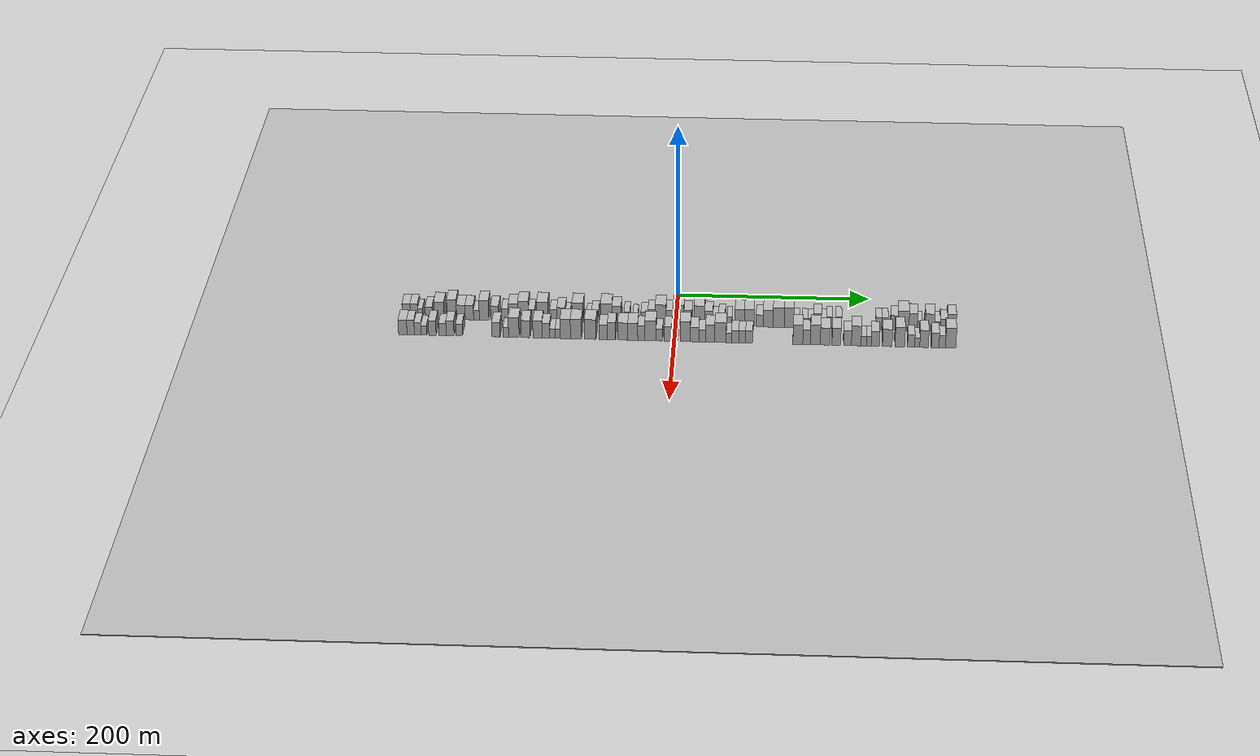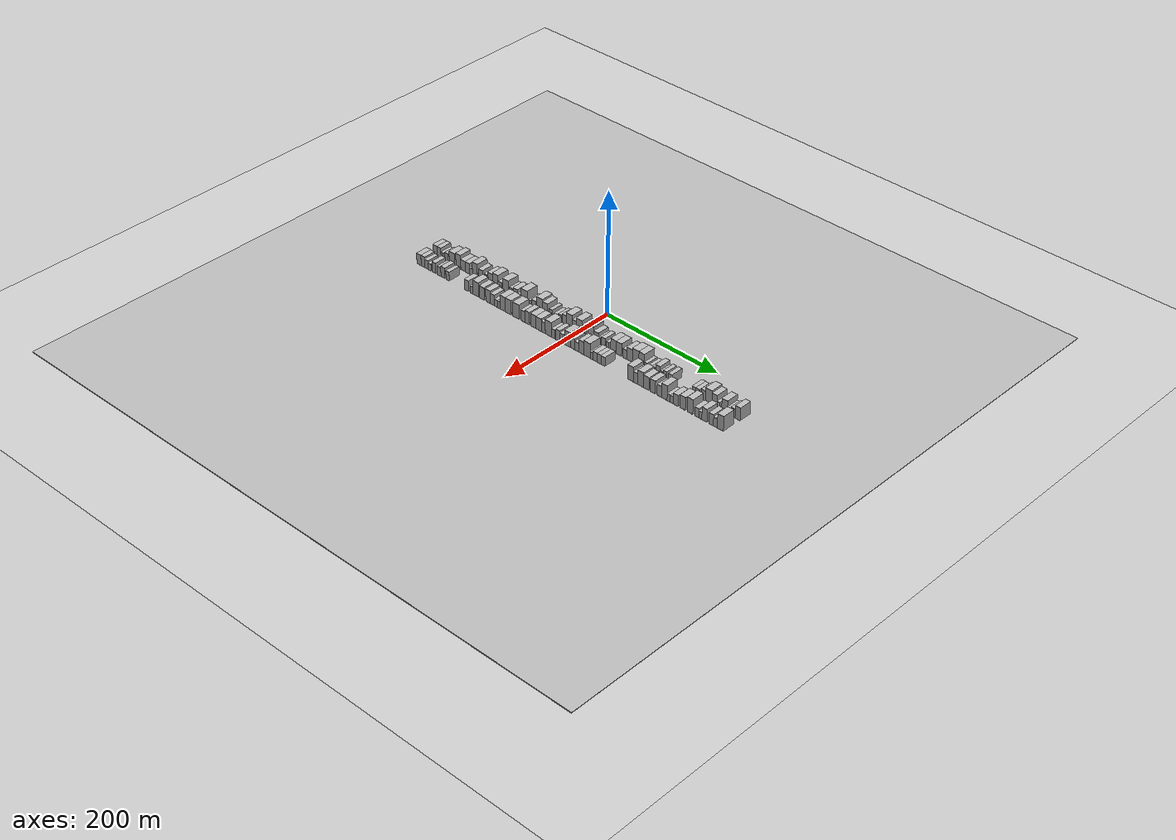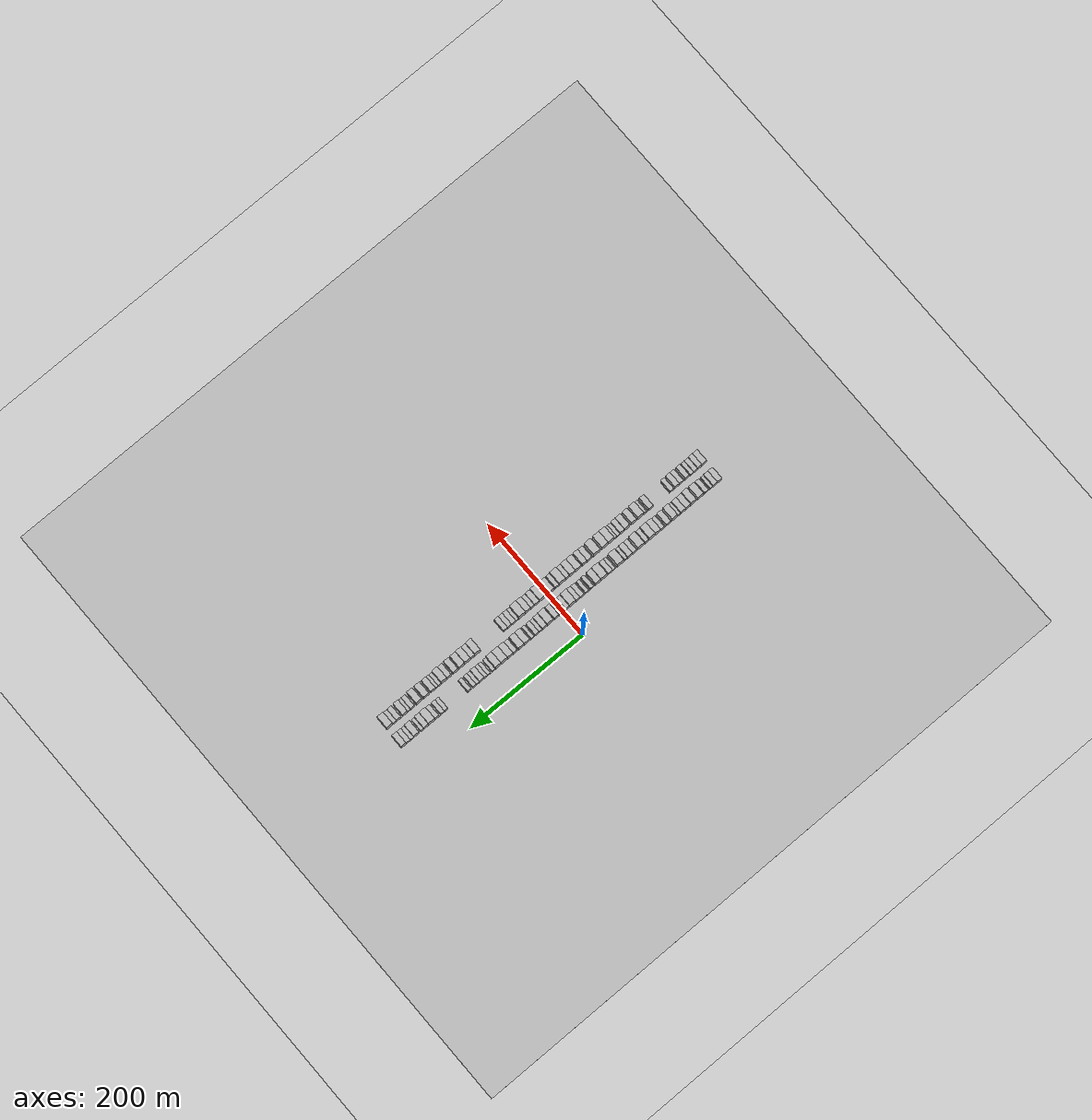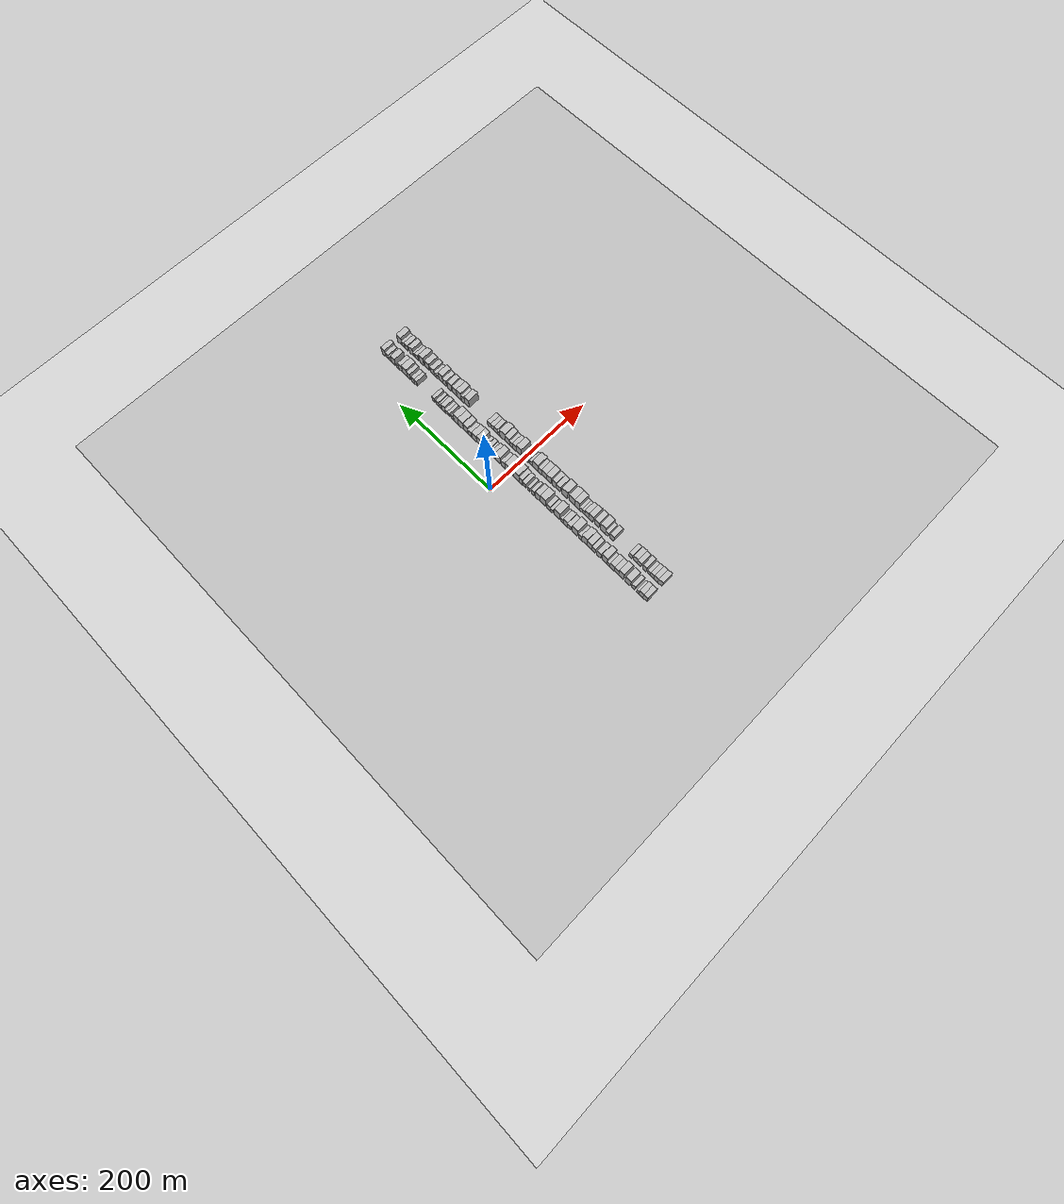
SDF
<?xml version="1.0" encoding="utf-8"?>

<sdf version="1.6">

   <world name="default">

      <gui fullscreen="0">

         <camera name="user_camera">

            <pose>-15 0 4.57585 0 0 0</pose>

            <view_controller>orbit</view_controller>

         </camera>

      </gui>

      <scene>

         <sky>

           <clouds>

             <speed>12</speed>

           </clouds>

         </sky>

         <ambient>0.4 0.4 0.4 1</ambient>

         <background>0.7 0.7 0.7 1</background>

         <shadows>1</shadows>

      </scene>

      <gravity>0 0 -9.8066</gravity>

      <magnetic_field>6e-06 2.3e-05 -4.2e-05</magnetic_field>

      <physics default="0" name="default_physics" type="ode">

         <ode>

            <solver>

               <type>quick</type>

               <iters>10</iters>

               <sor>1.0</sor>

               <use_dynamic_moi_rescaling>0</use_dynamic_moi_rescaling>

            </solver>

            <constraints>

               <cfm>0</cfm>

               <erp>0.2</erp>

               <contact_max_correcting_vel>100</contact_max_correcting_vel>

               <contact_surface_layer>0.001</contact_surface_layer>

            </constraints>

         </ode>

         <max_step_size>0.004</max_step_size>

         <real_time_factor>1</real_time_factor>

         <real_time_update_rate>250</real_time_update_rate>

      </physics>

      <light name="sun" type="directional">

         <cast_shadows>1</cast_shadows>

         <pose>0 0 10 0 0 0</pose>

         <diffuse>0.8 0.8 0.8 1</diffuse>

         <specular>0.2 0.2 0.2 1</specular>

         <attenuation>

            <range>1000</range>

            <constant>0.9</constant>

            <linear>0.01</linear>

            <quadratic>0.001</quadratic>

         </attenuation>

         <direction>-0.5 0.1 -0.9</direction>

      </light>

      <include>

         <name>ground_plane_1</name>

         <uri>model://HANNAS_ground_plane</uri>

         <pose>0 0 0  0 0 0</pose>

      </include>

      <include>

         <name>ground_plane_2</name>

         <uri>model://HANNAS_ground_plane</uri>

         <pose>100 0 0  0 0 0</pose>

      </include>

      <model name="building_1">

         <static>1</static>

         <pose frame="">50.0000 -279.8190 0 0.000000 0.000000 0.000000</pose>

         <link name="link">

            <pose frame="">0 0 9.00 0 0 0</pose>

            <collision name="collision">

               <geometry>

                  <box>

                     <size>20.0000 8.3619 18.0000</size>

                  </box>

               </geometry>

               <max_contacts>10</max_contacts>

               <surface>

                  <contact>

                     <ode/>

                  </contact>

                  <bounce/>

                  <friction>

                     <torsional>

                        <ode/>

                     </torsional>

                     <ode/>

                  </friction>

               </surface>

            </collision>

            <visual name="visual">

               <cast_shadows>0</cast_shadows>

               <geometry>

                  <box>

                     <size>20.0000 8.3619 18.0000</size>

                  </box>

               </geometry>

               <material>

                  <script>

                     <uri>model://HANNAS_wall/materials/scripts</uri>

                     <uri>model://HANNAS_wall/materials/textures</uri>

                     <name>vrc/HANNAS_wall</name>

                  </script>

               </material>

            </visual>

            <self_collide>0</self_collide>

            <enable_wind>0</enable_wind>

            <kinematic>0</kinematic>

         </link>

      </model>

      <model name="building_2">

         <static>1</static>

         <pose frame="">50.0000 -271.7829 0 0.000000 0.000000 0.000000</pose>

         <link name="link">

            <pose frame="">0 0 9.00 0 0 0</pose>

            <collision name="collision">

               <geometry>

                  <box>

                     <size>20.0000 7.7102 18.0000</size>

                  </box>

               </geometry>

               <max_contacts>10</max_contacts>

               <surface>

                  <contact>

                     <ode/>

                  </contact>

                  <bounce/>

                  <friction>

                     <torsional>

                        <ode/>

                     </torsional>

                     <ode/>

                  </friction>

               </surface>

            </collision>

            <visual name="visual">

               <cast_shadows>0</cast_shadows>

               <geometry>

                  <box>

                     <size>20.0000 7.7102 18.0000</size>

                  </box>

               </geometry>

               <material>

                  <script>

                     <uri>model://HANNAS_wall/materials/scripts</uri>

                     <uri>model://HANNAS_wall/materials/textures</uri>

                     <name>vrc/HANNAS_wall</name>

                  </script>

               </material>

            </visual>

            <self_collide>0</self_collide>

            <enable_wind>0</enable_wind>

            <kinematic>0</kinematic>

         </link>

      </model>

      <model name="building_3">

         <static>1</static>

         <pose frame="">50.0000 -265.4402 0 0.000000 0.000000 0.000000</pose>

         <link name="link">

            <pose frame="">0 0 6.00 0 0 0</pose>

            <collision name="collision">

               <geometry>

                  <box>

                     <size>20.0000 4.9754 12.0000</size>

                  </box>

               </geometry>

               <max_contacts>10</max_contacts>

               <surface>

                  <contact>

                     <ode/>

                  </contact>

                  <bounce/>

                  <friction>

                     <torsional>

                        <ode/>

                     </torsional>

                     <ode/>

                  </friction>

               </surface>

            </collision>

            <visual name="visual">

               <cast_shadows>0</cast_shadows>

               <geometry>

                  <box>

                     <size>20.0000 4.9754 12.0000</size>

                  </box>

               </geometry>

               <material>

                  <script>

                     <uri>model://HANNAS_wall/materials/scripts</uri>

                     <uri>model://HANNAS_wall/materials/textures</uri>

                     <name>vrc/HANNAS_wall</name>

                  </script>

               </material>

            </visual>

            <self_collide>0</self_collide>

            <enable_wind>0</enable_wind>

            <kinematic>0</kinematic>

         </link>

      </model>

      <model name="building_4">

         <static>1</static>

         <pose frame="">50.0000 -256.4035 0 0.000000 0.000000 0.000000</pose>

         <link name="link">

            <pose frame="">0 0 7.50 0 0 0</pose>

            <collision name="collision">

               <geometry>

                  <box>

                     <size>20.0000 7.0979 15.0000</size>

                  </box>

               </geometry>

               <max_contacts>10</max_contacts>

               <surface>

                  <contact>

                     <ode/>

                  </contact>

                  <bounce/>

                  <friction>

                     <torsional>

                        <ode/>

                     </torsional>

                     <ode/>

                  </friction>

               </surface>

            </collision>

            <visual name="visual">

               <cast_shadows>0</cast_shadows>

               <geometry>

                  <box>

                     <size>20.0000 7.0979 15.0000</size>

                  </box>

               </geometry>

               <material>

                  <script>

                     <uri>model://HANNAS_wall/materials/scripts</uri>

                     <uri>model://HANNAS_wall/materials/textures</uri>

                     <name>vrc/HANNAS_wall</name>

                  </script>

               </material>

            </visual>

            <self_collide>0</self_collide>

            <enable_wind>0</enable_wind>

            <kinematic>0</kinematic>

         </link>

      </model>

      <model name="building_5">

         <static>1</static>

         <pose frame="">50.0000 -245.6082 0 0.000000 0.000000 0.000000</pose>

         <link name="link">

            <pose frame="">0 0 10.50 0 0 0</pose>

            <collision name="collision">

               <geometry>

                  <box>

                     <size>20.0000 10.4927 21.0000</size>

                  </box>

               </geometry>

               <max_contacts>10</max_contacts>

               <surface>

                  <contact>

                     <ode/>

                  </contact>

                  <bounce/>

                  <friction>

                     <torsional>

                        <ode/>

                     </torsional>

                     <ode/>

                  </friction>

               </surface>

            </collision>

            <visual name="visual">

               <cast_shadows>0</cast_shadows>

               <geometry>

                  <box>

                     <size>20.0000 10.4927 21.0000</size>

                  </box>

               </geometry>

               <material>

                  <script>

                     <uri>model://HANNAS_wall/materials/scripts</uri>

                     <uri>model://HANNAS_wall/materials/textures</uri>

                     <name>vrc/HANNAS_wall</name>

                  </script>

               </material>

            </visual>

            <self_collide>0</self_collide>

            <enable_wind>0</enable_wind>

            <kinematic>0</kinematic>

         </link>

      </model>

      <model name="building_6">

         <static>1</static>

         <pose frame="">50.0000 -232.4707 0 0.000000 0.000000 0.000000</pose>

         <link name="link">

            <pose frame="">0 0 12.00 0 0 0</pose>

            <collision name="collision">

               <geometry>

                  <box>

                     <size>20.0000 9.7823 24.0000</size>

                  </box>

               </geometry>

               <max_contacts>10</max_contacts>

               <surface>

                  <contact>

                     <ode/>

                  </contact>

                  <bounce/>

                  <friction>

                     <torsional>

                        <ode/>

                     </torsional>

                     <ode/>

                  </friction>

               </surface>

            </collision>

            <visual name="visual">

               <cast_shadows>0</cast_shadows>

               <geometry>

                  <box>

                     <size>20.0000 9.7823 24.0000</size>

                  </box>

               </geometry>

               <material>

                  <script>

                     <uri>model://HANNAS_wall/materials/scripts</uri>

                     <uri>model://HANNAS_wall/materials/textures</uri>

                     <name>vrc/HANNAS_wall</name>

                  </script>

               </material>

            </visual>

            <self_collide>0</self_collide>

            <enable_wind>0</enable_wind>

            <kinematic>0</kinematic>

         </link>

      </model>

      <model name="building_7">

         <static>1</static>

         <pose frame="">50.0000 -223.0820 0 0.000000 0.000000 0.000000</pose>

         <link name="link">

            <pose frame="">0 0 9.00 0 0 0</pose>

            <collision name="collision">

               <geometry>

                  <box>

                     <size>20.0000 8.9953 18.0000</size>

                  </box>

               </geometry>

               <max_contacts>10</max_contacts>

               <surface>

                  <contact>

                     <ode/>

                  </contact>

                  <bounce/>

                  <friction>

                     <torsional>

                        <ode/>

                     </torsional>

                     <ode/>

                  </friction>

               </surface>

            </collision>

            <visual name="visual">

               <cast_shadows>0</cast_shadows>

               <geometry>

                  <box>

                     <size>20.0000 8.9953 18.0000</size>

                  </box>

               </geometry>

               <material>

                  <script>

                     <uri>model://HANNAS_wall/materials/scripts</uri>

                     <uri>model://HANNAS_wall/materials/textures</uri>

                     <name>vrc/HANNAS_wall</name>

                  </script>

               </material>

            </visual>

            <self_collide>0</self_collide>

            <enable_wind>0</enable_wind>

            <kinematic>0</kinematic>

         </link>

      </model>

      <model name="building_8">

         <static>1</static>

         <pose frame="">50.0000 -214.2455 0 0.000000 0.000000 0.000000</pose>

         <link name="link">

            <pose frame="">0 0 9.00 0 0 0</pose>

            <collision name="collision">

               <geometry>

                  <box>

                     <size>20.0000 8.6777 18.0000</size>

                  </box>

               </geometry>

               <max_contacts>10</max_contacts>

               <surface>

                  <contact>

                     <ode/>

                  </contact>

                  <bounce/>

                  <friction>

                     <torsional>

                        <ode/>

                     </torsional>

                     <ode/>

                  </friction>

               </surface>

            </collision>

            <visual name="visual">

               <cast_shadows>0</cast_shadows>

               <geometry>

                  <box>

                     <size>20.0000 8.6777 18.0000</size>

                  </box>

               </geometry>

               <material>

                  <script>

                     <uri>model://HANNAS_wall/materials/scripts</uri>

                     <uri>model://HANNAS_wall/materials/textures</uri>

                     <name>vrc/HANNAS_wall</name>

                  </script>

               </material>

            </visual>

            <self_collide>0</self_collide>

            <enable_wind>0</enable_wind>

            <kinematic>0</kinematic>

         </link>

      </model>

      <model name="building_9">

         <static>1</static>

         <pose frame="">50.0000 -206.9102 0 0.000000 0.000000 0.000000</pose>

         <link name="link">

            <pose frame="">0 0 6.00 0 0 0</pose>

            <collision name="collision">

               <geometry>

                  <box>

                     <size>20.0000 5.9929 12.0000</size>

                  </box>

               </geometry>

               <max_contacts>10</max_contacts>

               <surface>

                  <contact>

                     <ode/>

                  </contact>

                  <bounce/>

                  <friction>

                     <torsional>

                        <ode/>

                     </torsional>

                     <ode/>

                  </friction>

               </surface>

            </collision>

            <visual name="visual">

               <cast_shadows>0</cast_shadows>

               <geometry>

                  <box>

                     <size>20.0000 5.9929 12.0000</size>

                  </box>

               </geometry>

               <material>

                  <script>

                     <uri>model://HANNAS_wall/materials/scripts</uri>

                     <uri>model://HANNAS_wall/materials/textures</uri>

                     <name>vrc/HANNAS_wall</name>

                  </script>

               </material>

            </visual>

            <self_collide>0</self_collide>

            <enable_wind>0</enable_wind>

            <kinematic>0</kinematic>

         </link>

      </model>

      <model name="building_10">

         <static>1</static>

         <pose frame="">50.0000 -198.9653 0 0.000000 0.000000 0.000000</pose>

         <link name="link">

            <pose frame="">0 0 12.00 0 0 0</pose>

            <collision name="collision">

               <geometry>

                  <box>

                     <size>20.0000 9.8969 24.0000</size>

                  </box>

               </geometry>

               <max_contacts>10</max_contacts>

               <surface>

                  <contact>

                     <ode/>

                  </contact>

                  <bounce/>

                  <friction>

                     <torsional>

                        <ode/>

                     </torsional>

                     <ode/>

                  </friction>

               </surface>

            </collision>

            <visual name="visual">

               <cast_shadows>0</cast_shadows>

               <geometry>

                  <box>

                     <size>20.0000 9.8969 24.0000</size>

                  </box>

               </geometry>

               <material>

                  <script>

                     <uri>model://HANNAS_wall/materials/scripts</uri>

                     <uri>model://HANNAS_wall/materials/textures</uri>

                     <name>vrc/HANNAS_wall</name>

                  </script>

               </material>

            </visual>

            <self_collide>0</self_collide>

            <enable_wind>0</enable_wind>

            <kinematic>0</kinematic>

         </link>

      </model>

      <model name="building_11">

         <static>1</static>

         <pose frame="">50.0000 -187.8194 0 0.000000 0.000000 0.000000</pose>

         <link name="link">

            <pose frame="">0 0 9.00 0 0 0</pose>

            <collision name="collision">

               <geometry>

                  <box>

                     <size>20.0000 8.3949 18.0000</size>

                  </box>

               </geometry>

               <max_contacts>10</max_contacts>

               <surface>

                  <contact>

                     <ode/>

                  </contact>

                  <bounce/>

                  <friction>

                     <torsional>

                        <ode/>

                     </torsional>

                     <ode/>

                  </friction>

               </surface>

            </collision>

            <visual name="visual">

               <cast_shadows>0</cast_shadows>

               <geometry>

                  <box>

                     <size>20.0000 8.3949 18.0000</size>

                  </box>

               </geometry>

               <material>

                  <script>

                     <uri>model://HANNAS_wall/materials/scripts</uri>

                     <uri>model://HANNAS_wall/materials/textures</uri>

                     <name>vrc/HANNAS_wall</name>

                  </script>

               </material>

            </visual>

            <self_collide>0</self_collide>

            <enable_wind>0</enable_wind>

            <kinematic>0</kinematic>

         </link>

      </model>

      <model name="building_12">

         <static>1</static>

         <pose frame="">50.0000 -177.0867 0 0.000000 0.000000 0.000000</pose>

         <link name="link">

            <pose frame="">0 0 7.50 0 0 0</pose>

            <collision name="collision">

               <geometry>

                  <box>

                     <size>20.0000 7.0706 15.0000</size>

                  </box>

               </geometry>

               <max_contacts>10</max_contacts>

               <surface>

                  <contact>

                     <ode/>

                  </contact>

                  <bounce/>

                  <friction>

                     <torsional>

                        <ode/>

                     </torsional>

                     <ode/>

                  </friction>

               </surface>

            </collision>

            <visual name="visual">

               <cast_shadows>0</cast_shadows>

               <geometry>

                  <box>

                     <size>20.0000 7.0706 15.0000</size>

                  </box>

               </geometry>

               <material>

                  <script>

                     <uri>model://HANNAS_wall/materials/scripts</uri>

                     <uri>model://HANNAS_wall/materials/textures</uri>

                     <name>vrc/HANNAS_wall</name>

                  </script>

               </material>

            </visual>

            <self_collide>0</self_collide>

            <enable_wind>0</enable_wind>

            <kinematic>0</kinematic>

         </link>

      </model>

      <model name="building_13">

         <static>1</static>

         <pose frame="">50.0000 -168.6290 0 0.000000 0.000000 0.000000</pose>

         <link name="link">

            <pose frame="">0 0 10.50 0 0 0</pose>

            <collision name="collision">

               <geometry>

                  <box>

                     <size>20.0000 9.8448 21.0000</size>

                  </box>

               </geometry>

               <max_contacts>10</max_contacts>

               <surface>

                  <contact>

                     <ode/>

                  </contact>

                  <bounce/>

                  <friction>

                     <torsional>

                        <ode/>

                     </torsional>

                     <ode/>

                  </friction>

               </surface>

            </collision>

            <visual name="visual">

               <cast_shadows>0</cast_shadows>

               <geometry>

                  <box>

                     <size>20.0000 9.8448 21.0000</size>

                  </box>

               </geometry>

               <material>

                  <script>

                     <uri>model://HANNAS_wall/materials/scripts</uri>

                     <uri>model://HANNAS_wall/materials/textures</uri>

                     <name>vrc/HANNAS_wall</name>

                  </script>

               </material>

            </visual>

            <self_collide>0</self_collide>

            <enable_wind>0</enable_wind>

            <kinematic>0</kinematic>

         </link>

      </model>

      <model name="building_14">

         <static>1</static>

         <pose frame="">50.0000 -158.3106 0 0.000000 0.000000 0.000000</pose>

         <link name="link">

            <pose frame="">0 0 12.00 0 0 0</pose>

            <collision name="collision">

               <geometry>

                  <box>

                     <size>20.0000 10.7921 24.0000</size>

                  </box>

               </geometry>

               <max_contacts>10</max_contacts>

               <surface>

                  <contact>

                     <ode/>

                  </contact>

                  <bounce/>

                  <friction>

                     <torsional>

                        <ode/>

                     </torsional>

                     <ode/>

                  </friction>

               </surface>

            </collision>

            <visual name="visual">

               <cast_shadows>0</cast_shadows>

               <geometry>

                  <box>

                     <size>20.0000 10.7921 24.0000</size>

                  </box>

               </geometry>

               <material>

                  <script>

                     <uri>model://HANNAS_wall/materials/scripts</uri>

                     <uri>model://HANNAS_wall/materials/textures</uri>

                     <name>vrc/HANNAS_wall</name>

                  </script>

               </material>

            </visual>

            <self_collide>0</self_collide>

            <enable_wind>0</enable_wind>

            <kinematic>0</kinematic>

         </link>

      </model>

      <model name="building_15">

         <static>1</static>

         <pose frame="">50.0000 -149.5389 0 0.000000 0.000000 0.000000</pose>

         <link name="link">

            <pose frame="">0 0 7.50 0 0 0</pose>

            <collision name="collision">

               <geometry>

                  <box>

                     <size>20.0000 6.7513 15.0000</size>

                  </box>

               </geometry>

               <max_contacts>10</max_contacts>

               <surface>

                  <contact>

                     <ode/>

                  </contact>

                  <bounce/>

                  <friction>

                     <torsional>

                        <ode/>

                     </torsional>

                     <ode/>

                  </friction>

               </surface>

            </collision>

            <visual name="visual">

               <cast_shadows>0</cast_shadows>

               <geometry>

                  <box>

                     <size>20.0000 6.7513 15.0000</size>

                  </box>

               </geometry>

               <material>

                  <script>

                     <uri>model://HANNAS_wall/materials/scripts</uri>

                     <uri>model://HANNAS_wall/materials/textures</uri>

                     <name>vrc/HANNAS_wall</name>

                  </script>

               </material>

            </visual>

            <self_collide>0</self_collide>

            <enable_wind>0</enable_wind>

            <kinematic>0</kinematic>

         </link>

      </model>

      <model name="building_16">

         <static>1</static>

         <pose frame="">50.0000 -138.3980 0 0.000000 0.000000 0.000000</pose>

         <link name="link">

            <pose frame="">0 0 12.00 0 0 0</pose>

            <collision name="collision">

               <geometry>

                  <box>

                     <size>20.0000 11.5305 24.0000</size>

                  </box>

               </geometry>

               <max_contacts>10</max_contacts>

               <surface>

                  <contact>

                     <ode/>

                  </contact>

                  <bounce/>

                  <friction>

                     <torsional>

                        <ode/>

                     </torsional>

                     <ode/>

                  </friction>

               </surface>

            </collision>

            <visual name="visual">

               <cast_shadows>0</cast_shadows>

               <geometry>

                  <box>

                     <size>20.0000 11.5305 24.0000</size>

                  </box>

               </geometry>

               <material>

                  <script>

                     <uri>model://HANNAS_wall/materials/scripts</uri>

                     <uri>model://HANNAS_wall/materials/textures</uri>

                     <name>vrc/HANNAS_wall</name>

                  </script>

               </material>

            </visual>

            <self_collide>0</self_collide>

            <enable_wind>0</enable_wind>

            <kinematic>0</kinematic>

         </link>

      </model>

      <model name="building_17">

         <static>1</static>

         <pose frame="">50.0000 -126.9144 0 0.000000 0.000000 0.000000</pose>

         <link name="link">

            <pose frame="">0 0 7.50 0 0 0</pose>

            <collision name="collision">

               <geometry>

                  <box>

                     <size>20.0000 7.4367 15.0000</size>

                  </box>

               </geometry>

               <max_contacts>10</max_contacts>

               <surface>

                  <contact>

                     <ode/>

                  </contact>

                  <bounce/>

                  <friction>

                     <torsional>

                        <ode/>

                     </torsional>

                     <ode/>

                  </friction>

               </surface>

            </collision>

            <visual name="visual">

               <cast_shadows>0</cast_shadows>

               <geometry>

                  <box>

                     <size>20.0000 7.4367 15.0000</size>

                  </box>

               </geometry>

               <material>

                  <script>

                     <uri>model://HANNAS_wall/materials/scripts</uri>

                     <uri>model://HANNAS_wall/materials/textures</uri>

                     <name>vrc/HANNAS_wall</name>

                  </script>

               </material>

            </visual>

            <self_collide>0</self_collide>

            <enable_wind>0</enable_wind>

            <kinematic>0</kinematic>

         </link>

      </model>

      <model name="building_18">

         <static>1</static>

         <pose frame="">50.0000 -118.8978 0 0.000000 0.000000 0.000000</pose>

         <link name="link">

            <pose frame="">0 0 9.00 0 0 0</pose>

            <collision name="collision">

               <geometry>

                  <box>

                     <size>20.0000 8.5964 18.0000</size>

                  </box>

               </geometry>

               <max_contacts>10</max_contacts>

               <surface>

                  <contact>

                     <ode/>

                  </contact>

                  <bounce/>

                  <friction>

                     <torsional>

                        <ode/>

                     </torsional>

                     <ode/>

                  </friction>

               </surface>

            </collision>

            <visual name="visual">

               <cast_shadows>0</cast_shadows>

               <geometry>

                  <box>

                     <size>20.0000 8.5964 18.0000</size>

                  </box>

               </geometry>

               <material>

                  <script>

                     <uri>model://HANNAS_wall/materials/scripts</uri>

                     <uri>model://HANNAS_wall/materials/textures</uri>

                     <name>vrc/HANNAS_wall</name>

                  </script>

               </material>

            </visual>

            <self_collide>0</self_collide>

            <enable_wind>0</enable_wind>

            <kinematic>0</kinematic>

         </link>

      </model>

      <model name="building_19">

         <static>1</static>

         <pose frame="">50.0000 -112.0478 0 0.000000 0.000000 0.000000</pose>

         <link name="link">

            <pose frame="">0 0 6.00 0 0 0</pose>

            <collision name="collision">

               <geometry>

                  <box>

                     <size>20.0000 5.1036 12.0000</size>

                  </box>

               </geometry>

               <max_contacts>10</max_contacts>

               <surface>

                  <contact>

                     <ode/>

                  </contact>

                  <bounce/>

                  <friction>

                     <torsional>

                        <ode/>

                     </torsional>

                     <ode/>

                  </friction>

               </surface>

            </collision>

            <visual name="visual">

               <cast_shadows>0</cast_shadows>

               <geometry>

                  <box>

                     <size>20.0000 5.1036 12.0000</size>

                  </box>

               </geometry>

               <material>

                  <script>

                     <uri>model://HANNAS_wall/materials/scripts</uri>

                     <uri>model://HANNAS_wall/materials/textures</uri>

                     <name>vrc/HANNAS_wall</name>

                  </script>

               </material>

            </visual>

            <self_collide>0</self_collide>

            <enable_wind>0</enable_wind>

            <kinematic>0</kinematic>

         </link>

      </model>

      <model name="building_20">

         <static>1</static>

         <pose frame="">50.0000 -101.6275 0 0.000000 0.000000 0.000000</pose>

         <link name="link">

            <pose frame="">0 0 12.00 0 0 0</pose>

            <collision name="collision">

               <geometry>

                  <box>

                     <size>20.0000 11.7370 24.0000</size>

                  </box>

               </geometry>

               <max_contacts>10</max_contacts>

               <surface>

                  <contact>

                     <ode/>

                  </contact>

                  <bounce/>

                  <friction>

                     <torsional>

                        <ode/>

                     </torsional>

                     <ode/>

                  </friction>

               </surface>

            </collision>

            <visual name="visual">

               <cast_shadows>0</cast_shadows>

               <geometry>

                  <box>

                     <size>20.0000 11.7370 24.0000</size>

                  </box>

               </geometry>

               <material>

                  <script>

                     <uri>model://HANNAS_wall/materials/scripts</uri>

                     <uri>model://HANNAS_wall/materials/textures</uri>

                     <name>vrc/HANNAS_wall</name>

                  </script>

               </material>

            </visual>

            <self_collide>0</self_collide>

            <enable_wind>0</enable_wind>

            <kinematic>0</kinematic>

         </link>

      </model>

      <model name="building_21">

         <static>1</static>

         <pose frame="">50.0000 -90.0536 0 0.000000 0.000000 0.000000</pose>

         <link name="link">

            <pose frame="">0 0 6.00 0 0 0</pose>

            <collision name="collision">

               <geometry>

                  <box>

                     <size>20.0000 5.4109 12.0000</size>

                  </box>

               </geometry>

               <max_contacts>10</max_contacts>

               <surface>

                  <contact>

                     <ode/>

                  </contact>

                  <bounce/>

                  <friction>

                     <torsional>

                        <ode/>

                     </torsional>

                     <ode/>

                  </friction>

               </surface>

            </collision>

            <visual name="visual">

               <cast_shadows>0</cast_shadows>

               <geometry>

                  <box>

                     <size>20.0000 5.4109 12.0000</size>

                  </box>

               </geometry>

               <material>

                  <script>

                     <uri>model://HANNAS_wall/materials/scripts</uri>

                     <uri>model://HANNAS_wall/materials/textures</uri>

                     <name>vrc/HANNAS_wall</name>

                  </script>

               </material>

            </visual>

            <self_collide>0</self_collide>

            <enable_wind>0</enable_wind>

            <kinematic>0</kinematic>

         </link>

      </model>

      <model name="building_22">

         <static>1</static>

         <pose frame="">50.0000 -83.6219 0 0.000000 0.000000 0.000000</pose>

         <link name="link">

            <pose frame="">0 0 7.50 0 0 0</pose>

            <collision name="collision">

               <geometry>

                  <box>

                     <size>20.0000 7.4524 15.0000</size>

                  </box>

               </geometry>

               <max_contacts>10</max_contacts>

               <surface>

                  <contact>

                     <ode/>

                  </contact>

                  <bounce/>

                  <friction>

                     <torsional>

                        <ode/>

                     </torsional>

                     <ode/>

                  </friction>

               </surface>

            </collision>

            <visual name="visual">

               <cast_shadows>0</cast_shadows>

               <geometry>

                  <box>

                     <size>20.0000 7.4524 15.0000</size>

                  </box>

               </geometry>

               <material>

                  <script>

                     <uri>model://HANNAS_wall/materials/scripts</uri>

                     <uri>model://HANNAS_wall/materials/textures</uri>

                     <name>vrc/HANNAS_wall</name>

                  </script>

               </material>

            </visual>

            <self_collide>0</self_collide>

            <enable_wind>0</enable_wind>

            <kinematic>0</kinematic>

         </link>

      </model>

      <model name="building_23">

         <static>1</static>

         <pose frame="">50.0000 -72.0594 0 0.000000 0.000000 0.000000</pose>

         <link name="link">

            <pose frame="">0 0 12.00 0 0 0</pose>

            <collision name="collision">

               <geometry>

                  <box>

                     <size>20.0000 11.6725 24.0000</size>

                  </box>

               </geometry>

               <max_contacts>10</max_contacts>

               <surface>

                  <contact>

                     <ode/>

                  </contact>

                  <bounce/>

                  <friction>

                     <torsional>

                        <ode/>

                     </torsional>

                     <ode/>

                  </friction>

               </surface>

            </collision>

            <visual name="visual">

               <cast_shadows>0</cast_shadows>

               <geometry>

                  <box>

                     <size>20.0000 11.6725 24.0000</size>

                  </box>

               </geometry>

               <material>

                  <script>

                     <uri>model://HANNAS_wall/materials/scripts</uri>

                     <uri>model://HANNAS_wall/materials/textures</uri>

                     <name>vrc/HANNAS_wall</name>

                  </script>

               </material>

            </visual>

            <self_collide>0</self_collide>

            <enable_wind>0</enable_wind>

            <kinematic>0</kinematic>

         </link>

      </model>

      <model name="building_24">

         <static>1</static>

         <pose frame="">50.0000 -61.4678 0 0.000000 0.000000 0.000000</pose>

         <link name="link">

            <pose frame="">0 0 10.50 0 0 0</pose>

            <collision name="collision">

               <geometry>

                  <box>

                     <size>20.0000 9.5107 21.0000</size>

                  </box>

               </geometry>

               <max_contacts>10</max_contacts>

               <surface>

                  <contact>

                     <ode/>

                  </contact>

                  <bounce/>

                  <friction>

                     <torsional>

                        <ode/>

                     </torsional>

                     <ode/>

                  </friction>

               </surface>

            </collision>

            <visual name="visual">

               <cast_shadows>0</cast_shadows>

               <geometry>

                  <box>

                     <size>20.0000 9.5107 21.0000</size>

                  </box>

               </geometry>

               <material>

                  <script>

                     <uri>model://HANNAS_wall/materials/scripts</uri>

                     <uri>model://HANNAS_wall/materials/textures</uri>

                     <name>vrc/HANNAS_wall</name>

                  </script>

               </material>

            </visual>

            <self_collide>0</self_collide>

            <enable_wind>0</enable_wind>

            <kinematic>0</kinematic>

         </link>

      </model>

      <model name="building_25">

         <static>1</static>

         <pose frame="">50.0000 -50.6916 0 0.000000 0.000000 0.000000</pose>

         <link name="link">

            <pose frame="">0 0 7.50 0 0 0</pose>

            <collision name="collision">

               <geometry>

                  <box>

                     <size>20.0000 6.0417 15.0000</size>

                  </box>

               </geometry>

               <max_contacts>10</max_contacts>

               <surface>

                  <contact>

                     <ode/>

                  </contact>

                  <bounce/>

                  <friction>

                     <torsional>

                        <ode/>

                     </torsional>

                     <ode/>

                  </friction>

               </surface>

            </collision>

            <visual name="visual">

               <cast_shadows>0</cast_shadows>

               <geometry>

                  <box>

                     <size>20.0000 6.0417 15.0000</size>

                  </box>

               </geometry>

               <material>

                  <script>

                     <uri>model://HANNAS_wall/materials/scripts</uri>

                     <uri>model://HANNAS_wall/materials/textures</uri>

                     <name>vrc/HANNAS_wall</name>

                  </script>

               </material>

            </visual>

            <self_collide>0</self_collide>

            <enable_wind>0</enable_wind>

            <kinematic>0</kinematic>

         </link>

      </model>

      <model name="building_26">

         <static>1</static>

         <pose frame="">50.0000 -41.9416 0 0.000000 0.000000 0.000000</pose>

         <link name="link">

            <pose frame="">0 0 6.00 0 0 0</pose>

            <collision name="collision">

               <geometry>

                  <box>

                     <size>20.0000 5.4582 12.0000</size>

                  </box>

               </geometry>

               <max_contacts>10</max_contacts>

               <surface>

                  <contact>

                     <ode/>

                  </contact>

                  <bounce/>

                  <friction>

                     <torsional>

                        <ode/>

                     </torsional>

                     <ode/>

                  </friction>

               </surface>

            </collision>

            <visual name="visual">

               <cast_shadows>0</cast_shadows>

               <geometry>

                  <box>

                     <size>20.0000 5.4582 12.0000</size>

                  </box>

               </geometry>

               <material>

                  <script>

                     <uri>model://HANNAS_wall/materials/scripts</uri>

                     <uri>model://HANNAS_wall/materials/textures</uri>

                     <name>vrc/HANNAS_wall</name>

                  </script>

               </material>

            </visual>

            <self_collide>0</self_collide>

            <enable_wind>0</enable_wind>

            <kinematic>0</kinematic>

         </link>

      </model>

      <model name="building_27">

         <static>1</static>

         <pose frame="">50.0000 -32.5497 0 0.000000 0.000000 0.000000</pose>

         <link name="link">

            <pose frame="">0 0 7.50 0 0 0</pose>

            <collision name="collision">

               <geometry>

                  <box>

                     <size>20.0000 7.3256 15.0000</size>

                  </box>

               </geometry>

               <max_contacts>10</max_contacts>

               <surface>

                  <contact>

                     <ode/>

                  </contact>

                  <bounce/>

                  <friction>

                     <torsional>

                        <ode/>

                     </torsional>

                     <ode/>

                  </friction>

               </surface>

            </collision>

            <visual name="visual">

               <cast_shadows>0</cast_shadows>

               <geometry>

                  <box>

                     <size>20.0000 7.3256 15.0000</size>

                  </box>

               </geometry>

               <material>

                  <script>

                     <uri>model://HANNAS_wall/materials/scripts</uri>

                     <uri>model://HANNAS_wall/materials/textures</uri>

                     <name>vrc/HANNAS_wall</name>

                  </script>

               </material>

            </visual>

            <self_collide>0</self_collide>

            <enable_wind>0</enable_wind>

            <kinematic>0</kinematic>

         </link>

      </model>

      <model name="building_28">

         <static>1</static>

         <pose frame="">50.0000 -25.1557 0 0.000000 0.000000 0.000000</pose>

         <link name="link">

            <pose frame="">0 0 9.00 0 0 0</pose>

            <collision name="collision">

               <geometry>

                  <box>

                     <size>20.0000 7.4624 18.0000</size>

                  </box>

               </geometry>

               <max_contacts>10</max_contacts>

               <surface>

                  <contact>

                     <ode/>

                  </contact>

                  <bounce/>

                  <friction>

                     <torsional>

                        <ode/>

                     </torsional>

                     <ode/>

                  </friction>

               </surface>

            </collision>

            <visual name="visual">

               <cast_shadows>0</cast_shadows>

               <geometry>

                  <box>

                     <size>20.0000 7.4624 18.0000</size>

                  </box>

               </geometry>

               <material>

                  <script>

                     <uri>model://HANNAS_wall/materials/scripts</uri>

                     <uri>model://HANNAS_wall/materials/textures</uri>

                     <name>vrc/HANNAS_wall</name>

                  </script>

               </material>

            </visual>

            <self_collide>0</self_collide>

            <enable_wind>0</enable_wind>

            <kinematic>0</kinematic>

         </link>

      </model>

      <model name="building_29">

         <static>1</static>

         <pose frame="">50.0000 -15.7782 0 0.000000 0.000000 0.000000</pose>

         <link name="link">

            <pose frame="">0 0 12.00 0 0 0</pose>

            <collision name="collision">

               <geometry>

                  <box>

                     <size>20.0000 11.2925 24.0000</size>

                  </box>

               </geometry>

               <max_contacts>10</max_contacts>

               <surface>

                  <contact>

                     <ode/>

                  </contact>

                  <bounce/>

                  <friction>

                     <torsional>

                        <ode/>

                     </torsional>

                     <ode/>

                  </friction>

               </surface>

            </collision>

            <visual name="visual">

               <cast_shadows>0</cast_shadows>

               <geometry>

                  <box>

                     <size>20.0000 11.2925 24.0000</size>

                  </box>

               </geometry>

               <material>

                  <script>

                     <uri>model://HANNAS_wall/materials/scripts</uri>

                     <uri>model://HANNAS_wall/materials/textures</uri>

                     <name>vrc/HANNAS_wall</name>

                  </script>

               </material>

            </visual>

            <self_collide>0</self_collide>

            <enable_wind>0</enable_wind>

            <kinematic>0</kinematic>

         </link>

      </model>

      <model name="building_30">

         <static>1</static>

         <pose frame="">50.0000 -6.4503 0 0.000000 0.000000 0.000000</pose>

         <link name="link">

            <pose frame="">0 0 9.00 0 0 0</pose>

            <collision name="collision">

               <geometry>

                  <box>

                     <size>20.0000 7.3634 18.0000</size>

                  </box>

               </geometry>

               <max_contacts>10</max_contacts>

               <surface>

                  <contact>

                     <ode/>

                  </contact>

                  <bounce/>

                  <friction>

                     <torsional>

                        <ode/>

                     </torsional>

                     <ode/>

                  </friction>

               </surface>

            </collision>

            <visual name="visual">

               <cast_shadows>0</cast_shadows>

               <geometry>

                  <box>

                     <size>20.0000 7.3634 18.0000</size>

                  </box>

               </geometry>

               <material>

                  <script>

                     <uri>model://HANNAS_wall/materials/scripts</uri>

                     <uri>model://HANNAS_wall/materials/textures</uri>

                     <name>vrc/HANNAS_wall</name>

                  </script>

               </material>

            </visual>

            <self_collide>0</self_collide>

            <enable_wind>0</enable_wind>

            <kinematic>0</kinematic>

         </link>

      </model>

      <model name="building_31">

         <static>1</static>

         <pose frame="">50.0000 2.8149 0 0.000000 0.000000 0.000000</pose>

         <link name="link">

            <pose frame="">0 0 12.00 0 0 0</pose>

            <collision name="collision">

               <geometry>

                  <box>

                     <size>20.0000 11.1670 24.0000</size>

                  </box>

               </geometry>

               <max_contacts>10</max_contacts>

               <surface>

                  <contact>

                     <ode/>

                  </contact>

                  <bounce/>

                  <friction>

                     <torsional>

                        <ode/>

                     </torsional>

                     <ode/>

                  </friction>

               </surface>

            </collision>

            <visual name="visual">

               <cast_shadows>0</cast_shadows>

               <geometry>

                  <box>

                     <size>20.0000 11.1670 24.0000</size>

                  </box>

               </geometry>

               <material>

                  <script>

                     <uri>model://HANNAS_wall/materials/scripts</uri>

                     <uri>model://HANNAS_wall/materials/textures</uri>

                     <name>vrc/HANNAS_wall</name>

                  </script>

               </material>

            </visual>

            <self_collide>0</self_collide>

            <enable_wind>0</enable_wind>

            <kinematic>0</kinematic>

         </link>

      </model>

      <model name="building_32">

         <static>1</static>

         <pose frame="">50.0000 12.5977 0 0.000000 0.000000 0.000000</pose>

         <link name="link">

            <pose frame="">0 0 9.00 0 0 0</pose>

            <collision name="collision">

               <geometry>

                  <box>

                     <size>20.0000 8.3987 18.0000</size>

                  </box>

               </geometry>

               <max_contacts>10</max_contacts>

               <surface>

                  <contact>

                     <ode/>

                  </contact>

                  <bounce/>

                  <friction>

                     <torsional>

                        <ode/>

                     </torsional>

                     <ode/>

                  </friction>

               </surface>

            </collision>

            <visual name="visual">

               <cast_shadows>0</cast_shadows>

               <geometry>

                  <box>

                     <size>20.0000 8.3987 18.0000</size>

                  </box>

               </geometry>

               <material>

                  <script>

                     <uri>model://HANNAS_wall/materials/scripts</uri>

                     <uri>model://HANNAS_wall/materials/textures</uri>

                     <name>vrc/HANNAS_wall</name>

                  </script>

               </material>

            </visual>

            <self_collide>0</self_collide>

            <enable_wind>0</enable_wind>

            <kinematic>0</kinematic>

         </link>

      </model>

      <model name="building_33">

         <static>1</static>

         <pose frame="">50.0000 24.3071 0 0.000000 0.000000 0.000000</pose>

         <link name="link">

            <pose frame="">0 0 12.00 0 0 0</pose>

            <collision name="collision">

               <geometry>

                  <box>

                     <size>20.0000 11.0200 24.0000</size>

                  </box>

               </geometry>

               <max_contacts>10</max_contacts>

               <surface>

                  <contact>

                     <ode/>

                  </contact>

                  <bounce/>

                  <friction>

                     <torsional>

                        <ode/>

                     </torsional>

                     <ode/>

                  </friction>

               </surface>

            </collision>

            <visual name="visual">

               <cast_shadows>0</cast_shadows>

               <geometry>

                  <box>

                     <size>20.0000 11.0200 24.0000</size>

                  </box>

               </geometry>

               <material>

                  <script>

                     <uri>model://HANNAS_wall/materials/scripts</uri>

                     <uri>model://HANNAS_wall/materials/textures</uri>

                     <name>vrc/HANNAS_wall</name>

                  </script>

               </material>

            </visual>

            <self_collide>0</self_collide>

            <enable_wind>0</enable_wind>

            <kinematic>0</kinematic>

         </link>

      </model>

      <model name="building_34">

         <static>1</static>

         <pose frame="">50.0000 34.0459 0 0.000000 0.000000 0.000000</pose>

         <link name="link">

            <pose frame="">0 0 9.00 0 0 0</pose>

            <collision name="collision">

               <geometry>

                  <box>

                     <size>20.0000 8.4576 18.0000</size>

                  </box>

               </geometry>

               <max_contacts>10</max_contacts>

               <surface>

                  <contact>

                     <ode/>

                  </contact>

                  <bounce/>

                  <friction>

                     <torsional>

                        <ode/>

                     </torsional>

                     <ode/>

                  </friction>

               </surface>

            </collision>

            <visual name="visual">

               <cast_shadows>0</cast_shadows>

               <geometry>

                  <box>

                     <size>20.0000 8.4576 18.0000</size>

                  </box>

               </geometry>

               <material>

                  <script>

                     <uri>model://HANNAS_wall/materials/scripts</uri>

                     <uri>model://HANNAS_wall/materials/textures</uri>

                     <name>vrc/HANNAS_wall</name>

                  </script>

               </material>

            </visual>

            <self_collide>0</self_collide>

            <enable_wind>0</enable_wind>

            <kinematic>0</kinematic>

         </link>

      </model>

      <model name="building_35">

         <static>1</static>

         <pose frame="">50.0000 41.2181 0 0.000000 0.000000 0.000000</pose>

         <link name="link">

            <pose frame="">0 0 6.00 0 0 0</pose>

            <collision name="collision">

               <geometry>

                  <box>

                     <size>20.0000 5.8868 12.0000</size>

                  </box>

               </geometry>

               <max_contacts>10</max_contacts>

               <surface>

                  <contact>

                     <ode/>

                  </contact>

                  <bounce/>

                  <friction>

                     <torsional>

                        <ode/>

                     </torsional>

                     <ode/>

                  </friction>

               </surface>

            </collision>

            <visual name="visual">

               <cast_shadows>0</cast_shadows>

               <geometry>

                  <box>

                     <size>20.0000 5.8868 12.0000</size>

                  </box>

               </geometry>

               <material>

                  <script>

                     <uri>model://HANNAS_wall/materials/scripts</uri>

                     <uri>model://HANNAS_wall/materials/textures</uri>

                     <name>vrc/HANNAS_wall</name>

                  </script>

               </material>

            </visual>

            <self_collide>0</self_collide>

            <enable_wind>0</enable_wind>

            <kinematic>0</kinematic>

         </link>

      </model>

      <model name="building_36">

         <static>1</static>

         <pose frame="">50.0000 47.5665 0 0.000000 0.000000 0.000000</pose>

         <link name="link">

            <pose frame="">0 0 7.50 0 0 0</pose>

            <collision name="collision">

               <geometry>

                  <box>

                     <size>20.0000 6.8100 15.0000</size>

                  </box>

               </geometry>

               <max_contacts>10</max_contacts>

               <surface>

                  <contact>

                     <ode/>

                  </contact>

                  <bounce/>

                  <friction>

                     <torsional>

                        <ode/>

                     </torsional>

                     <ode/>

                  </friction>

               </surface>

            </collision>

            <visual name="visual">

               <cast_shadows>0</cast_shadows>

               <geometry>

                  <box>

                     <size>20.0000 6.8100 15.0000</size>

                  </box>

               </geometry>

               <material>

                  <script>

                     <uri>model://HANNAS_wall/materials/scripts</uri>

                     <uri>model://HANNAS_wall/materials/textures</uri>

                     <name>vrc/HANNAS_wall</name>

                  </script>

               </material>

            </visual>

            <self_collide>0</self_collide>

            <enable_wind>0</enable_wind>

            <kinematic>0</kinematic>

         </link>

      </model>

      <model name="building_37">

         <static>1</static>

         <pose frame="">50.0000 55.5154 0 0.000000 0.000000 0.000000</pose>

         <link name="link">

            <pose frame="">0 0 6.00 0 0 0</pose>

            <collision name="collision">

               <geometry>

                  <box>

                     <size>20.0000 5.0878 12.0000</size>

                  </box>

               </geometry>

               <max_contacts>10</max_contacts>

               <surface>

                  <contact>

                     <ode/>

                  </contact>

                  <bounce/>

                  <friction>

                     <torsional>

                        <ode/>

                     </torsional>

                     <ode/>

                  </friction>

               </surface>

            </collision>

            <visual name="visual">

               <cast_shadows>0</cast_shadows>

               <geometry>

                  <box>

                     <size>20.0000 5.0878 12.0000</size>

                  </box>

               </geometry>

               <material>

                  <script>

                     <uri>model://HANNAS_wall/materials/scripts</uri>

                     <uri>model://HANNAS_wall/materials/textures</uri>

                     <name>vrc/HANNAS_wall</name>

                  </script>

               </material>

            </visual>

            <self_collide>0</self_collide>

            <enable_wind>0</enable_wind>

            <kinematic>0</kinematic>

         </link>

      </model>

      <model name="building_38">

         <static>1</static>

         <pose frame="">50.0000 66.0061 0 0.000000 0.000000 0.000000</pose>

         <link name="link">

            <pose frame="">0 0 10.50 0 0 0</pose>

            <collision name="collision">

               <geometry>

                  <box>

                     <size>20.0000 9.8937 21.0000</size>

                  </box>

               </geometry>

               <max_contacts>10</max_contacts>

               <surface>

                  <contact>

                     <ode/>

                  </contact>

                  <bounce/>

                  <friction>

                     <torsional>

                        <ode/>

                     </torsional>

                     <ode/>

                  </friction>

               </surface>

            </collision>

            <visual name="visual">

               <cast_shadows>0</cast_shadows>

               <geometry>

                  <box>

                     <size>20.0000 9.8937 21.0000</size>

                  </box>

               </geometry>

               <material>

                  <script>

                     <uri>model://HANNAS_wall/materials/scripts</uri>

                     <uri>model://HANNAS_wall/materials/textures</uri>

                     <name>vrc/HANNAS_wall</name>

                  </script>

               </material>

            </visual>

            <self_collide>0</self_collide>

            <enable_wind>0</enable_wind>

            <kinematic>0</kinematic>

         </link>

      </model>

      <model name="building_39">

         <static>1</static>

         <pose frame="">50.0000 75.9395 0 0.000000 0.000000 0.000000</pose>

         <link name="link">

            <pose frame="">0 0 10.50 0 0 0</pose>

            <collision name="collision">

               <geometry>

                  <box>

                     <size>20.0000 9.9730 21.0000</size>

                  </box>

               </geometry>

               <max_contacts>10</max_contacts>

               <surface>

                  <contact>

                     <ode/>

                  </contact>

                  <bounce/>

                  <friction>

                     <torsional>

                        <ode/>

                     </torsional>

                     <ode/>

                  </friction>

               </surface>

            </collision>

            <visual name="visual">

               <cast_shadows>0</cast_shadows>

               <geometry>

                  <box>

                     <size>20.0000 9.9730 21.0000</size>

                  </box>

               </geometry>

               <material>

                  <script>

                     <uri>model://HANNAS_wall/materials/scripts</uri>

                     <uri>model://HANNAS_wall/materials/textures</uri>

                     <name>vrc/HANNAS_wall</name>

                  </script>

               </material>

            </visual>

            <self_collide>0</self_collide>

            <enable_wind>0</enable_wind>

            <kinematic>0</kinematic>

         </link>

      </model>

      <model name="building_40">

         <static>1</static>

         <pose frame="">50.0000 86.6181 0 0.000000 0.000000 0.000000</pose>

         <link name="link">

            <pose frame="">0 0 7.50 0 0 0</pose>

            <collision name="collision">

               <geometry>

                  <box>

                     <size>20.0000 7.3843 15.0000</size>

                  </box>

               </geometry>

               <max_contacts>10</max_contacts>

               <surface>

                  <contact>

                     <ode/>

                  </contact>

                  <bounce/>

                  <friction>

                     <torsional>

                        <ode/>

                     </torsional>

                     <ode/>

                  </friction>

               </surface>

            </collision>

            <visual name="visual">

               <cast_shadows>0</cast_shadows>

               <geometry>

                  <box>

                     <size>20.0000 7.3843 15.0000</size>

                  </box>

               </geometry>

               <material>

                  <script>

                     <uri>model://HANNAS_wall/materials/scripts</uri>

                     <uri>model://HANNAS_wall/materials/textures</uri>

                     <name>vrc/HANNAS_wall</name>

                  </script>

               </material>

            </visual>

            <self_collide>0</self_collide>

            <enable_wind>0</enable_wind>

            <kinematic>0</kinematic>

         </link>

      </model>

      <model name="building_41">

         <static>1</static>

         <pose frame="">50.0000 95.3826 0 0.000000 0.000000 0.000000</pose>

         <link name="link">

            <pose frame="">0 0 10.50 0 0 0</pose>

            <collision name="collision">

               <geometry>

                  <box>

                     <size>20.0000 10.1447 21.0000</size>

                  </box>

               </geometry>

               <max_contacts>10</max_contacts>

               <surface>

                  <contact>

                     <ode/>

                  </contact>

                  <bounce/>

                  <friction>

                     <torsional>

                        <ode/>

                     </torsional>

                     <ode/>

                  </friction>

               </surface>

            </collision>

            <visual name="visual">

               <cast_shadows>0</cast_shadows>

               <geometry>

                  <box>

                     <size>20.0000 10.1447 21.0000</size>

                  </box>

               </geometry>

               <material>

                  <script>

                     <uri>model://HANNAS_wall/materials/scripts</uri>

                     <uri>model://HANNAS_wall/materials/textures</uri>

                     <name>vrc/HANNAS_wall</name>

                  </script>

               </material>

            </visual>

            <self_collide>0</self_collide>

            <enable_wind>0</enable_wind>

            <kinematic>0</kinematic>

         </link>

      </model>

      <model name="building_42">

         <static>1</static>

         <pose frame="">50.0000 106.2034 0 0.000000 0.000000 0.000000</pose>

         <link name="link">

            <pose frame="">0 0 12.00 0 0 0</pose>

            <collision name="collision">

               <geometry>

                  <box>

                     <size>20.0000 11.4968 24.0000</size>

                  </box>

               </geometry>

               <max_contacts>10</max_contacts>

               <surface>

                  <contact>

                     <ode/>

                  </contact>

                  <bounce/>

                  <friction>

                     <torsional>

                        <ode/>

                     </torsional>

                     <ode/>

                  </friction>

               </surface>

            </collision>

            <visual name="visual">

               <cast_shadows>0</cast_shadows>

               <geometry>

                  <box>

                     <size>20.0000 11.4968 24.0000</size>

                  </box>

               </geometry>

               <material>

                  <script>

                     <uri>model://HANNAS_wall/materials/scripts</uri>

                     <uri>model://HANNAS_wall/materials/textures</uri>

                     <name>vrc/HANNAS_wall</name>

                  </script>

               </material>

            </visual>

            <self_collide>0</self_collide>

            <enable_wind>0</enable_wind>

            <kinematic>0</kinematic>

         </link>

      </model>

      <model name="building_43">

         <static>1</static>

         <pose frame="">50.0000 117.0278 0 0.000000 0.000000 0.000000</pose>

         <link name="link">

            <pose frame="">0 0 12.00 0 0 0</pose>

            <collision name="collision">

               <geometry>

                  <box>

                     <size>20.0000 10.1520 24.0000</size>

                  </box>

               </geometry>

               <max_contacts>10</max_contacts>

               <surface>

                  <contact>

                     <ode/>

                  </contact>

                  <bounce/>

                  <friction>

                     <torsional>

                        <ode/>

                     </torsional>

                     <ode/>

                  </friction>

               </surface>

            </collision>

            <visual name="visual">

               <cast_shadows>0</cast_shadows>

               <geometry>

                  <box>

                     <size>20.0000 10.1520 24.0000</size>

                  </box>

               </geometry>

               <material>

                  <script>

                     <uri>model://HANNAS_wall/materials/scripts</uri>

                     <uri>model://HANNAS_wall/materials/textures</uri>

                     <name>vrc/HANNAS_wall</name>

                  </script>

               </material>

            </visual>

            <self_collide>0</self_collide>

            <enable_wind>0</enable_wind>

            <kinematic>0</kinematic>

         </link>

      </model>

      <model name="building_44">

         <static>1</static>

         <pose frame="">50.0000 124.8269 0 0.000000 0.000000 0.000000</pose>

         <link name="link">

            <pose frame="">0 0 6.00 0 0 0</pose>

            <collision name="collision">

               <geometry>

                  <box>

                     <size>20.0000 5.4463 12.0000</size>

                  </box>

               </geometry>

               <max_contacts>10</max_contacts>

               <surface>

                  <contact>

                     <ode/>

                  </contact>

                  <bounce/>

                  <friction>

                     <torsional>

                        <ode/>

                     </torsional>

                     <ode/>

                  </friction>

               </surface>

            </collision>

            <visual name="visual">

               <cast_shadows>0</cast_shadows>

               <geometry>

                  <box>

                     <size>20.0000 5.4463 12.0000</size>

                  </box>

               </geometry>

               <material>

                  <script>

                     <uri>model://HANNAS_wall/materials/scripts</uri>

                     <uri>model://HANNAS_wall/materials/textures</uri>

                     <name>vrc/HANNAS_wall</name>

                  </script>

               </material>

            </visual>

            <self_collide>0</self_collide>

            <enable_wind>0</enable_wind>

            <kinematic>0</kinematic>

         </link>

      </model>

      <model name="building_45">

         <static>1</static>

         <pose frame="">50.0000 133.2887 0 0.000000 0.000000 0.000000</pose>

         <link name="link">

            <pose frame="">0 0 6.00 0 0 0</pose>

            <collision name="collision">

               <geometry>

                  <box>

                     <size>20.0000 5.4773 12.0000</size>

                  </box>

               </geometry>

               <max_contacts>10</max_contacts>

               <surface>

                  <contact>

                     <ode/>

                  </contact>

                  <bounce/>

                  <friction>

                     <torsional>

                        <ode/>

                     </torsional>

                     <ode/>

                  </friction>

               </surface>

            </collision>

            <visual name="visual">

               <cast_shadows>0</cast_shadows>

               <geometry>

                  <box>

                     <size>20.0000 5.4773 12.0000</size>

                  </box>

               </geometry>

               <material>

                  <script>

                     <uri>model://HANNAS_wall/materials/scripts</uri>

                     <uri>model://HANNAS_wall/materials/textures</uri>

                     <name>vrc/HANNAS_wall</name>

                  </script>

               </material>

            </visual>

            <self_collide>0</self_collide>

            <enable_wind>0</enable_wind>

            <kinematic>0</kinematic>

         </link>

      </model>

      <model name="building_46">

         <static>1</static>

         <pose frame="">50.0000 138.9892 0 0.000000 0.000000 0.000000</pose>

         <link name="link">

            <pose frame="">0 0 6.00 0 0 0</pose>

            <collision name="collision">

               <geometry>

                  <box>

                     <size>20.0000 5.9235 12.0000</size>

                  </box>

               </geometry>

               <max_contacts>10</max_contacts>

               <surface>

                  <contact>

                     <ode/>

                  </contact>

                  <bounce/>

                  <friction>

                     <torsional>

                        <ode/>

                     </torsional>

                     <ode/>

                  </friction>

               </surface>

            </collision>

            <visual name="visual">

               <cast_shadows>0</cast_shadows>

               <geometry>

                  <box>

                     <size>20.0000 5.9235 12.0000</size>

                  </box>

               </geometry>

               <material>

                  <script>

                     <uri>model://HANNAS_wall/materials/scripts</uri>

                     <uri>model://HANNAS_wall/materials/textures</uri>

                     <name>vrc/HANNAS_wall</name>

                  </script>

               </material>

            </visual>

            <self_collide>0</self_collide>

            <enable_wind>0</enable_wind>

            <kinematic>0</kinematic>

         </link>

      </model>

      <model name="building_47">

         <static>1</static>

         <pose frame="">50.0000 146.0393 0 0.000000 0.000000 0.000000</pose>

         <link name="link">

            <pose frame="">0 0 9.00 0 0 0</pose>

            <collision name="collision">

               <geometry>

                  <box>

                     <size>20.0000 8.1767 18.0000</size>

                  </box>

               </geometry>

               <max_contacts>10</max_contacts>

               <surface>

                  <contact>

                     <ode/>

                  </contact>

                  <bounce/>

                  <friction>

                     <torsional>

                        <ode/>

                     </torsional>

                     <ode/>

                  </friction>

               </surface>

            </collision>

            <visual name="visual">

               <cast_shadows>0</cast_shadows>

               <geometry>

                  <box>

                     <size>20.0000 8.1767 18.0000</size>

                  </box>

               </geometry>

               <material>

                  <script>

                     <uri>model://HANNAS_wall/materials/scripts</uri>

                     <uri>model://HANNAS_wall/materials/textures</uri>

                     <name>vrc/HANNAS_wall</name>

                  </script>

               </material>

            </visual>

            <self_collide>0</self_collide>

            <enable_wind>0</enable_wind>

            <kinematic>0</kinematic>

         </link>

      </model>

      <model name="building_48">

         <static>1</static>

         <pose frame="">50.0000 152.9805 0 0.000000 0.000000 0.000000</pose>

         <link name="link">

            <pose frame="">0 0 6.00 0 0 0</pose>

            <collision name="collision">

               <geometry>

                  <box>

                     <size>20.0000 5.7057 12.0000</size>

                  </box>

               </geometry>

               <max_contacts>10</max_contacts>

               <surface>

                  <contact>

                     <ode/>

                  </contact>

                  <bounce/>

                  <friction>

                     <torsional>

                        <ode/>

                     </torsional>

                     <ode/>

                  </friction>

               </surface>

            </collision>

            <visual name="visual">

               <cast_shadows>0</cast_shadows>

               <geometry>

                  <box>

                     <size>20.0000 5.7057 12.0000</size>

                  </box>

               </geometry>

               <material>

                  <script>

                     <uri>model://HANNAS_wall/materials/scripts</uri>

                     <uri>model://HANNAS_wall/materials/textures</uri>

                     <name>vrc/HANNAS_wall</name>

                  </script>

               </material>

            </visual>

            <self_collide>0</self_collide>

            <enable_wind>0</enable_wind>

            <kinematic>0</kinematic>

         </link>

      </model>

      <model name="building_49">

         <static>1</static>

         <pose frame="">50.0000 158.8335 0 0.000000 0.000000 0.000000</pose>

         <link name="link">

            <pose frame="">0 0 7.50 0 0 0</pose>

            <collision name="collision">

               <geometry>

                  <box>

                     <size>20.0000 6.0004 15.0000</size>

                  </box>

               </geometry>

               <max_contacts>10</max_contacts>

               <surface>

                  <contact>

                     <ode/>

                  </contact>

                  <bounce/>

                  <friction>

                     <torsional>

                        <ode/>

                     </torsional>

                     <ode/>

                  </friction>

               </surface>

            </collision>

            <visual name="visual">

               <cast_shadows>0</cast_shadows>

               <geometry>

                  <box>

                     <size>20.0000 6.0004 15.0000</size>

                  </box>

               </geometry>

               <material>

                  <script>

                     <uri>model://HANNAS_wall/materials/scripts</uri>

                     <uri>model://HANNAS_wall/materials/textures</uri>

                     <name>vrc/HANNAS_wall</name>

                  </script>

               </material>

            </visual>

            <self_collide>0</self_collide>

            <enable_wind>0</enable_wind>

            <kinematic>0</kinematic>

         </link>

      </model>

      <model name="building_50">

         <static>1</static>

         <pose frame="">50.0000 167.9812 0 0.000000 0.000000 0.000000</pose>

         <link name="link">

            <pose frame="">0 0 7.50 0 0 0</pose>

            <collision name="collision">

               <geometry>

                  <box>

                     <size>20.0000 6.2950 15.0000</size>

                  </box>

               </geometry>

               <max_contacts>10</max_contacts>

               <surface>

                  <contact>

                     <ode/>

                  </contact>

                  <bounce/>

                  <friction>

                     <torsional>

                        <ode/>

                     </torsional>

                     <ode/>

                  </friction>

               </surface>

            </collision>

            <visual name="visual">

               <cast_shadows>0</cast_shadows>

               <geometry>

                  <box>

                     <size>20.0000 6.2950 15.0000</size>

                  </box>

               </geometry>

               <material>

                  <script>

                     <uri>model://HANNAS_wall/materials/scripts</uri>

                     <uri>model://HANNAS_wall/materials/textures</uri>

                     <name>vrc/HANNAS_wall</name>

                  </script>

               </material>

            </visual>

            <self_collide>0</self_collide>

            <enable_wind>0</enable_wind>

            <kinematic>0</kinematic>

         </link>

      </model>

      <model name="building_51">

         <static>1</static>

         <pose frame="">50.0000 209.2563 0 0.000000 0.000000 0.000000</pose>

         <link name="link">

            <pose frame="">0 0 7.50 0 0 0</pose>

            <collision name="collision">

               <geometry>

                  <box>

                     <size>20.0000 6.0850 15.0000</size>

                  </box>

               </geometry>

               <max_contacts>10</max_contacts>

               <surface>

                  <contact>

                     <ode/>

                  </contact>

                  <bounce/>

                  <friction>

                     <torsional>

                        <ode/>

                     </torsional>

                     <ode/>

                  </friction>

               </surface>

            </collision>

            <visual name="visual">

               <cast_shadows>0</cast_shadows>

               <geometry>

                  <box>

                     <size>20.0000 6.0850 15.0000</size>

                  </box>

               </geometry>

               <material>

                  <script>

                     <uri>model://HANNAS_wall/materials/scripts</uri>

                     <uri>model://HANNAS_wall/materials/textures</uri>

                     <name>vrc/HANNAS_wall</name>

                  </script>

               </material>

            </visual>

            <self_collide>0</self_collide>

            <enable_wind>0</enable_wind>

            <kinematic>0</kinematic>

         </link>

      </model>

      <model name="building_52">

         <static>1</static>

         <pose frame="">50.0000 215.6219 0 0.000000 0.000000 0.000000</pose>

         <link name="link">

            <pose frame="">0 0 7.50 0 0 0</pose>

            <collision name="collision">

               <geometry>

                  <box>

                     <size>20.0000 6.6463 15.0000</size>

                  </box>

               </geometry>

               <max_contacts>10</max_contacts>

               <surface>

                  <contact>

                     <ode/>

                  </contact>

                  <bounce/>

                  <friction>

                     <torsional>

                        <ode/>

                     </torsional>

                     <ode/>

                  </friction>

               </surface>

            </collision>

            <visual name="visual">

               <cast_shadows>0</cast_shadows>

               <geometry>

                  <box>

                     <size>20.0000 6.6463 15.0000</size>

                  </box>

               </geometry>

               <material>

                  <script>

                     <uri>model://HANNAS_wall/materials/scripts</uri>

                     <uri>model://HANNAS_wall/materials/textures</uri>

                     <name>vrc/HANNAS_wall</name>

                  </script>

               </material>

            </visual>

            <self_collide>0</self_collide>

            <enable_wind>0</enable_wind>

            <kinematic>0</kinematic>

         </link>

      </model>

      <model name="building_53">

         <static>1</static>

         <pose frame="">50.0000 225.5456 0 0.000000 0.000000 0.000000</pose>

         <link name="link">

            <pose frame="">0 0 9.00 0 0 0</pose>

            <collision name="collision">

               <geometry>

                  <box>

                     <size>20.0000 7.2011 18.0000</size>

                  </box>

               </geometry>

               <max_contacts>10</max_contacts>

               <surface>

                  <contact>

                     <ode/>

                  </contact>

                  <bounce/>

                  <friction>

                     <torsional>

                        <ode/>

                     </torsional>

                     <ode/>

                  </friction>

               </surface>

            </collision>

            <visual name="visual">

               <cast_shadows>0</cast_shadows>

               <geometry>

                  <box>

                     <size>20.0000 7.2011 18.0000</size>

                  </box>

               </geometry>

               <material>

                  <script>

                     <uri>model://HANNAS_wall/materials/scripts</uri>

                     <uri>model://HANNAS_wall/materials/textures</uri>

                     <name>vrc/HANNAS_wall</name>

                  </script>

               </material>

            </visual>

            <self_collide>0</self_collide>

            <enable_wind>0</enable_wind>

            <kinematic>0</kinematic>

         </link>

      </model>

      <model name="building_54">

         <static>1</static>

         <pose frame="">50.0000 234.7607 0 0.000000 0.000000 0.000000</pose>

         <link name="link">

            <pose frame="">0 0 12.00 0 0 0</pose>

            <collision name="collision">

               <geometry>

                  <box>

                     <size>20.0000 11.2290 24.0000</size>

                  </box>

               </geometry>

               <max_contacts>10</max_contacts>

               <surface>

                  <contact>

                     <ode/>

                  </contact>

                  <bounce/>

                  <friction>

                     <torsional>

                        <ode/>

                     </torsional>

                     <ode/>

                  </friction>

               </surface>

            </collision>

            <visual name="visual">

               <cast_shadows>0</cast_shadows>

               <geometry>

                  <box>

                     <size>20.0000 11.2290 24.0000</size>

                  </box>

               </geometry>

               <material>

                  <script>

                     <uri>model://HANNAS_wall/materials/scripts</uri>

                     <uri>model://HANNAS_wall/materials/textures</uri>

                     <name>vrc/HANNAS_wall</name>

                  </script>

               </material>

            </visual>

            <self_collide>0</self_collide>

            <enable_wind>0</enable_wind>

            <kinematic>0</kinematic>

         </link>

      </model>

      <model name="building_55">

         <static>1</static>

         <pose frame="">50.0000 244.6903 0 0.000000 0.000000 0.000000</pose>

         <link name="link">

            <pose frame="">0 0 10.50 0 0 0</pose>

            <collision name="collision">

               <geometry>

                  <box>

                     <size>20.0000 8.6302 21.0000</size>

                  </box>

               </geometry>

               <max_contacts>10</max_contacts>

               <surface>

                  <contact>

                     <ode/>

                  </contact>

                  <bounce/>

                  <friction>

                     <torsional>

                        <ode/>

                     </torsional>

                     <ode/>

                  </friction>

               </surface>

            </collision>

            <visual name="visual">

               <cast_shadows>0</cast_shadows>

               <geometry>

                  <box>

                     <size>20.0000 8.6302 21.0000</size>

                  </box>

               </geometry>

               <material>

                  <script>

                     <uri>model://HANNAS_wall/materials/scripts</uri>

                     <uri>model://HANNAS_wall/materials/textures</uri>

                     <name>vrc/HANNAS_wall</name>

                  </script>

               </material>

            </visual>

            <self_collide>0</self_collide>

            <enable_wind>0</enable_wind>

            <kinematic>0</kinematic>

         </link>

      </model>

      <model name="building_56">

         <static>1</static>

         <pose frame="">50.0000 251.5346 0 0.000000 0.000000 0.000000</pose>

         <link name="link">

            <pose frame="">0 0 6.00 0 0 0</pose>

            <collision name="collision">

               <geometry>

                  <box>

                     <size>20.0000 5.0584 12.0000</size>

                  </box>

               </geometry>

               <max_contacts>10</max_contacts>

               <surface>

                  <contact>

                     <ode/>

                  </contact>

                  <bounce/>

                  <friction>

                     <torsional>

                        <ode/>

                     </torsional>

                     <ode/>

                  </friction>

               </surface>

            </collision>

            <visual name="visual">

               <cast_shadows>0</cast_shadows>

               <geometry>

                  <box>

                     <size>20.0000 5.0584 12.0000</size>

                  </box>

               </geometry>

               <material>

                  <script>

                     <uri>model://HANNAS_wall/materials/scripts</uri>

                     <uri>model://HANNAS_wall/materials/textures</uri>

                     <name>vrc/HANNAS_wall</name>

                  </script>

               </material>

            </visual>

            <self_collide>0</self_collide>

            <enable_wind>0</enable_wind>

            <kinematic>0</kinematic>

         </link>

      </model>

      <model name="building_57">

         <static>1</static>

         <pose frame="">50.0000 261.9085 0 0.000000 0.000000 0.000000</pose>

         <link name="link">

            <pose frame="">0 0 10.50 0 0 0</pose>

            <collision name="collision">

               <geometry>

                  <box>

                     <size>20.0000 9.6893 21.0000</size>

                  </box>

               </geometry>

               <max_contacts>10</max_contacts>

               <surface>

                  <contact>

                     <ode/>

                  </contact>

                  <bounce/>

                  <friction>

                     <torsional>

                        <ode/>

                     </torsional>

                     <ode/>

                  </friction>

               </surface>

            </collision>

            <visual name="visual">

               <cast_shadows>0</cast_shadows>

               <geometry>

                  <box>

                     <size>20.0000 9.6893 21.0000</size>

                  </box>

               </geometry>

               <material>

                  <script>

                     <uri>model://HANNAS_wall/materials/scripts</uri>

                     <uri>model://HANNAS_wall/materials/textures</uri>

                     <name>vrc/HANNAS_wall</name>

                  </script>

               </material>

            </visual>

            <self_collide>0</self_collide>

            <enable_wind>0</enable_wind>

            <kinematic>0</kinematic>

         </link>

      </model>

      <model name="building_58">

         <static>1</static>

         <pose frame="">50.0000 269.7282 0 0.000000 0.000000 0.000000</pose>

         <link name="link">

            <pose frame="">0 0 6.00 0 0 0</pose>

            <collision name="collision">

               <geometry>

                  <box>

                     <size>20.0000 5.9503 12.0000</size>

                  </box>

               </geometry>

               <max_contacts>10</max_contacts>

               <surface>

                  <contact>

                     <ode/>

                  </contact>

                  <bounce/>

                  <friction>

                     <torsional>

                        <ode/>

                     </torsional>

                     <ode/>

                  </friction>

               </surface>

            </collision>

            <visual name="visual">

               <cast_shadows>0</cast_shadows>

               <geometry>

                  <box>

                     <size>20.0000 5.9503 12.0000</size>

                  </box>

               </geometry>

               <material>

                  <script>

                     <uri>model://HANNAS_wall/materials/scripts</uri>

                     <uri>model://HANNAS_wall/materials/textures</uri>

                     <name>vrc/HANNAS_wall</name>

                  </script>

               </material>

            </visual>

            <self_collide>0</self_collide>

            <enable_wind>0</enable_wind>

            <kinematic>0</kinematic>

         </link>

      </model>

      <model name="building_59">

         <static>1</static>

         <pose frame="">50.0000 276.3991 0 0.000000 0.000000 0.000000</pose>

         <link name="link">

            <pose frame="">0 0 7.50 0 0 0</pose>

            <collision name="collision">

               <geometry>

                  <box>

                     <size>20.0000 7.3915 15.0000</size>

                  </box>

               </geometry>

               <max_contacts>10</max_contacts>

               <surface>

                  <contact>

                     <ode/>

                  </contact>

                  <bounce/>

                  <friction>

                     <torsional>

                        <ode/>

                     </torsional>

                     <ode/>

                  </friction>

               </surface>

            </collision>

            <visual name="visual">

               <cast_shadows>0</cast_shadows>

               <geometry>

                  <box>

                     <size>20.0000 7.3915 15.0000</size>

                  </box>

               </geometry>

               <material>

                  <script>

                     <uri>model://HANNAS_wall/materials/scripts</uri>

                     <uri>model://HANNAS_wall/materials/textures</uri>

                     <name>vrc/HANNAS_wall</name>

                  </script>

               </material>

            </visual>

            <self_collide>0</self_collide>

            <enable_wind>0</enable_wind>

            <kinematic>0</kinematic>

         </link>

      </model>

      <model name="building_60">

         <static>1</static>

         <pose frame="">50.0000 284.4112 0 0.000000 0.000000 0.000000</pose>

         <link name="link">

            <pose frame="">0 0 10.50 0 0 0</pose>

            <collision name="collision">

               <geometry>

                  <box>

                     <size>20.0000 8.6327 21.0000</size>

                  </box>

               </geometry>

               <max_contacts>10</max_contacts>

               <surface>

                  <contact>

                     <ode/>

                  </contact>

                  <bounce/>

                  <friction>

                     <torsional>

                        <ode/>

                     </torsional>

                     <ode/>

                  </friction>

               </surface>

            </collision>

            <visual name="visual">

               <cast_shadows>0</cast_shadows>

               <geometry>

                  <box>

                     <size>20.0000 8.6327 21.0000</size>

                  </box>

               </geometry>

               <material>

                  <script>

                     <uri>model://HANNAS_wall/materials/scripts</uri>

                     <uri>model://HANNAS_wall/materials/textures</uri>

                     <name>vrc/HANNAS_wall</name>

                  </script>

               </material>

            </visual>

            <self_collide>0</self_collide>

            <enable_wind>0</enable_wind>

            <kinematic>0</kinematic>

         </link>

      </model>

      <model name="building_61">

         <static>1</static>

         <pose frame="">82.0000 -279.6116 0 0.000000 0.000000 0.000000</pose>

         <link name="link">

            <pose frame="">0 0 9.00 0 0 0</pose>

            <collision name="collision">

               <geometry>

                  <box>

                     <size>20.0000 8.7768 18.0000</size>

                  </box>

               </geometry>

               <max_contacts>10</max_contacts>

               <surface>

                  <contact>

                     <ode/>

                  </contact>

                  <bounce/>

                  <friction>

                     <torsional>

                        <ode/>

                     </torsional>

                     <ode/>

                  </friction>

               </surface>

            </collision>

            <visual name="visual">

               <cast_shadows>0</cast_shadows>

               <geometry>

                  <box>

                     <size>20.0000 8.7768 18.0000</size>

                  </box>

               </geometry>

               <material>

                  <script>

                     <uri>model://HANNAS_wall/materials/scripts</uri>

                     <uri>model://HANNAS_wall/materials/textures</uri>

                     <name>vrc/HANNAS_wall</name>

                  </script>

               </material>

            </visual>

            <self_collide>0</self_collide>

            <enable_wind>0</enable_wind>

            <kinematic>0</kinematic>

         </link>

      </model>

      <model name="building_62">

         <static>1</static>

         <pose frame="">82.0000 -271.4348 0 0.000000 0.000000 0.000000</pose>

         <link name="link">

            <pose frame="">0 0 9.00 0 0 0</pose>

            <collision name="collision">

               <geometry>

                  <box>

                     <size>20.0000 7.5769 18.0000</size>

                  </box>

               </geometry>

               <max_contacts>10</max_contacts>

               <surface>

                  <contact>

                     <ode/>

                  </contact>

                  <bounce/>

                  <friction>

                     <torsional>

                        <ode/>

                     </torsional>

                     <ode/>

                  </friction>

               </surface>

            </collision>

            <visual name="visual">

               <cast_shadows>0</cast_shadows>

               <geometry>

                  <box>

                     <size>20.0000 7.5769 18.0000</size>

                  </box>

               </geometry>

               <material>

                  <script>

                     <uri>model://HANNAS_wall/materials/scripts</uri>

                     <uri>model://HANNAS_wall/materials/textures</uri>

                     <name>vrc/HANNAS_wall</name>

                  </script>

               </material>

            </visual>

            <self_collide>0</self_collide>

            <enable_wind>0</enable_wind>

            <kinematic>0</kinematic>

         </link>

      </model>

      <model name="building_63">

         <static>1</static>

         <pose frame="">82.0000 -264.1748 0 0.000000 0.000000 0.000000</pose>

         <link name="link">

            <pose frame="">0 0 7.50 0 0 0</pose>

            <collision name="collision">

               <geometry>

                  <box>

                     <size>20.0000 6.9432 15.0000</size>

                  </box>

               </geometry>

               <max_contacts>10</max_contacts>

               <surface>

                  <contact>

                     <ode/>

                  </contact>

                  <bounce/>

                  <friction>

                     <torsional>

                        <ode/>

                     </torsional>

                     <ode/>

                  </friction>

               </surface>

            </collision>

            <visual name="visual">

               <cast_shadows>0</cast_shadows>

               <geometry>

                  <box>

                     <size>20.0000 6.9432 15.0000</size>

                  </box>

               </geometry>

               <material>

                  <script>

                     <uri>model://HANNAS_wall/materials/scripts</uri>

                     <uri>model://HANNAS_wall/materials/textures</uri>

                     <name>vrc/HANNAS_wall</name>

                  </script>

               </material>

            </visual>

            <self_collide>0</self_collide>

            <enable_wind>0</enable_wind>

            <kinematic>0</kinematic>

         </link>

      </model>

      <model name="building_64">

         <static>1</static>

         <pose frame="">82.0000 -257.7788 0 0.000000 0.000000 0.000000</pose>

         <link name="link">

            <pose frame="">0 0 6.00 0 0 0</pose>

            <collision name="collision">

               <geometry>

                  <box>

                     <size>20.0000 5.8489 12.0000</size>

                  </box>

               </geometry>

               <max_contacts>10</max_contacts>

               <surface>

                  <contact>

                     <ode/>

                  </contact>

                  <bounce/>

                  <friction>

                     <torsional>

                        <ode/>

                     </torsional>

                     <ode/>

                  </friction>

               </surface>

            </collision>

            <visual name="visual">

               <cast_shadows>0</cast_shadows>

               <geometry>

                  <box>

                     <size>20.0000 5.8489 12.0000</size>

                  </box>

               </geometry>

               <material>

                  <script>

                     <uri>model://HANNAS_wall/materials/scripts</uri>

                     <uri>model://HANNAS_wall/materials/textures</uri>

                     <name>vrc/HANNAS_wall</name>

                  </script>

               </material>

            </visual>

            <self_collide>0</self_collide>

            <enable_wind>0</enable_wind>

            <kinematic>0</kinematic>

         </link>

      </model>

      <model name="building_65">

         <static>1</static>

         <pose frame="">82.0000 -249.0392 0 0.000000 0.000000 0.000000</pose>

         <link name="link">

            <pose frame="">0 0 9.00 0 0 0</pose>

            <collision name="collision">

               <geometry>

                  <box>

                     <size>20.0000 7.6304 18.0000</size>

                  </box>

               </geometry>

               <max_contacts>10</max_contacts>

               <surface>

                  <contact>

                     <ode/>

                  </contact>

                  <bounce/>

                  <friction>

                     <torsional>

                        <ode/>

                     </torsional>

                     <ode/>

                  </friction>

               </surface>

            </collision>

            <visual name="visual">

               <cast_shadows>0</cast_shadows>

               <geometry>

                  <box>

                     <size>20.0000 7.6304 18.0000</size>

                  </box>

               </geometry>

               <material>

                  <script>

                     <uri>model://HANNAS_wall/materials/scripts</uri>

                     <uri>model://HANNAS_wall/materials/textures</uri>

                     <name>vrc/HANNAS_wall</name>

                  </script>

               </material>

            </visual>

            <self_collide>0</self_collide>

            <enable_wind>0</enable_wind>

            <kinematic>0</kinematic>

         </link>

      </model>

      <model name="building_66">

         <static>1</static>

         <pose frame="">82.0000 -238.4993 0 0.000000 0.000000 0.000000</pose>

         <link name="link">

            <pose frame="">0 0 7.50 0 0 0</pose>

            <collision name="collision">

               <geometry>

                  <box>

                     <size>20.0000 7.4493 15.0000</size>

                  </box>

               </geometry>

               <max_contacts>10</max_contacts>

               <surface>

                  <contact>

                     <ode/>

                  </contact>

                  <bounce/>

                  <friction>

                     <torsional>

                        <ode/>

                     </torsional>

                     <ode/>

                  </friction>

               </surface>

            </collision>

            <visual name="visual">

               <cast_shadows>0</cast_shadows>

               <geometry>

                  <box>

                     <size>20.0000 7.4493 15.0000</size>

                  </box>

               </geometry>

               <material>

                  <script>

                     <uri>model://HANNAS_wall/materials/scripts</uri>

                     <uri>model://HANNAS_wall/materials/textures</uri>

                     <name>vrc/HANNAS_wall</name>

                  </script>

               </material>

            </visual>

            <self_collide>0</self_collide>

            <enable_wind>0</enable_wind>

            <kinematic>0</kinematic>

         </link>

      </model>

      <model name="building_67">

         <static>1</static>

         <pose frame="">82.0000 -230.7380 0 0.000000 0.000000 0.000000</pose>

         <link name="link">

            <pose frame="">0 0 9.00 0 0 0</pose>

            <collision name="collision">

               <geometry>

                  <box>

                     <size>20.0000 8.0734 18.0000</size>

                  </box>

               </geometry>

               <max_contacts>10</max_contacts>

               <surface>

                  <contact>

                     <ode/>

                  </contact>

                  <bounce/>

                  <friction>

                     <torsional>

                        <ode/>

                     </torsional>

                     <ode/>

                  </friction>

               </surface>

            </collision>

            <visual name="visual">

               <cast_shadows>0</cast_shadows>

               <geometry>

                  <box>

                     <size>20.0000 8.0734 18.0000</size>

                  </box>

               </geometry>

               <material>

                  <script>

                     <uri>model://HANNAS_wall/materials/scripts</uri>

                     <uri>model://HANNAS_wall/materials/textures</uri>

                     <name>vrc/HANNAS_wall</name>

                  </script>

               </material>

            </visual>

            <self_collide>0</self_collide>

            <enable_wind>0</enable_wind>

            <kinematic>0</kinematic>

         </link>

      </model>

      <model name="building_68">

         <static>1</static>

         <pose frame="">82.0000 -221.3300 0 0.000000 0.000000 0.000000</pose>

         <link name="link">

            <pose frame="">0 0 7.50 0 0 0</pose>

            <collision name="collision">

               <geometry>

                  <box>

                     <size>20.0000 6.7426 15.0000</size>

                  </box>

               </geometry>

               <max_contacts>10</max_contacts>

               <surface>

                  <contact>

                     <ode/>

                  </contact>

                  <bounce/>

                  <friction>

                     <torsional>

                        <ode/>

                     </torsional>

                     <ode/>

                  </friction>

               </surface>

            </collision>

            <visual name="visual">

               <cast_shadows>0</cast_shadows>

               <geometry>

                  <box>

                     <size>20.0000 6.7426 15.0000</size>

                  </box>

               </geometry>

               <material>

                  <script>

                     <uri>model://HANNAS_wall/materials/scripts</uri>

                     <uri>model://HANNAS_wall/materials/textures</uri>

                     <name>vrc/HANNAS_wall</name>

                  </script>

               </material>

            </visual>

            <self_collide>0</self_collide>

            <enable_wind>0</enable_wind>

            <kinematic>0</kinematic>

         </link>

      </model>

      <model name="building_69">

         <static>1</static>

         <pose frame="">82.0000 -183.3673 0 0.000000 0.000000 0.000000</pose>

         <link name="link">

            <pose frame="">0 0 9.00 0 0 0</pose>

            <collision name="collision">

               <geometry>

                  <box>

                     <size>20.0000 8.3942 18.0000</size>

                  </box>

               </geometry>

               <max_contacts>10</max_contacts>

               <surface>

                  <contact>

                     <ode/>

                  </contact>

                  <bounce/>

                  <friction>

                     <torsional>

                        <ode/>

                     </torsional>

                     <ode/>

                  </friction>

               </surface>

            </collision>

            <visual name="visual">

               <cast_shadows>0</cast_shadows>

               <geometry>

                  <box>

                     <size>20.0000 8.3942 18.0000</size>

                  </box>

               </geometry>

               <material>

                  <script>

                     <uri>model://HANNAS_wall/materials/scripts</uri>

                     <uri>model://HANNAS_wall/materials/textures</uri>

                     <name>vrc/HANNAS_wall</name>

                  </script>

               </material>

            </visual>

            <self_collide>0</self_collide>

            <enable_wind>0</enable_wind>

            <kinematic>0</kinematic>

         </link>

      </model>

      <model name="building_70">

         <static>1</static>

         <pose frame="">82.0000 -173.2988 0 0.000000 0.000000 0.000000</pose>

         <link name="link">

            <pose frame="">0 0 6.00 0 0 0</pose>

            <collision name="collision">

               <geometry>

                  <box>

                     <size>20.0000 5.7428 12.0000</size>

                  </box>

               </geometry>

               <max_contacts>10</max_contacts>

               <surface>

                  <contact>

                     <ode/>

                  </contact>

                  <bounce/>

                  <friction>

                     <torsional>

                        <ode/>

                     </torsional>

                     <ode/>

                  </friction>

               </surface>

            </collision>

            <visual name="visual">

               <cast_shadows>0</cast_shadows>

               <geometry>

                  <box>

                     <size>20.0000 5.7428 12.0000</size>

                  </box>

               </geometry>

               <material>

                  <script>

                     <uri>model://HANNAS_wall/materials/scripts</uri>

                     <uri>model://HANNAS_wall/materials/textures</uri>

                     <name>vrc/HANNAS_wall</name>

                  </script>

               </material>

            </visual>

            <self_collide>0</self_collide>

            <enable_wind>0</enable_wind>

            <kinematic>0</kinematic>

         </link>

      </model>

      <model name="building_71">

         <static>1</static>

         <pose frame="">82.0000 -164.9844 0 0.000000 0.000000 0.000000</pose>

         <link name="link">

            <pose frame="">0 0 12.00 0 0 0</pose>

            <collision name="collision">

               <geometry>

                  <box>

                     <size>20.0000 10.8860 24.0000</size>

                  </box>

               </geometry>

               <max_contacts>10</max_contacts>

               <surface>

                  <contact>

                     <ode/>

                  </contact>

                  <bounce/>

                  <friction>

                     <torsional>

                        <ode/>

                     </torsional>

                     <ode/>

                  </friction>

               </surface>

            </collision>

            <visual name="visual">

               <cast_shadows>0</cast_shadows>

               <geometry>

                  <box>

                     <size>20.0000 10.8860 24.0000</size>

                  </box>

               </geometry>

               <material>

                  <script>

                     <uri>model://HANNAS_wall/materials/scripts</uri>

                     <uri>model://HANNAS_wall/materials/textures</uri>

                     <name>vrc/HANNAS_wall</name>

                  </script>

               </material>

            </visual>

            <self_collide>0</self_collide>

            <enable_wind>0</enable_wind>

            <kinematic>0</kinematic>

         </link>

      </model>

      <model name="building_72">

         <static>1</static>

         <pose frame="">82.0000 -152.9470 0 0.000000 0.000000 0.000000</pose>

         <link name="link">

            <pose frame="">0 0 10.50 0 0 0</pose>

            <collision name="collision">

               <geometry>

                  <box>

                     <size>20.0000 9.1887 21.0000</size>

                  </box>

               </geometry>

               <max_contacts>10</max_contacts>

               <surface>

                  <contact>

                     <ode/>

                  </contact>

                  <bounce/>

                  <friction>

                     <torsional>

                        <ode/>

                     </torsional>

                     <ode/>

                  </friction>

               </surface>

            </collision>

            <visual name="visual">

               <cast_shadows>0</cast_shadows>

               <geometry>

                  <box>

                     <size>20.0000 9.1887 21.0000</size>

                  </box>

               </geometry>

               <material>

                  <script>

                     <uri>model://HANNAS_wall/materials/scripts</uri>

                     <uri>model://HANNAS_wall/materials/textures</uri>

                     <name>vrc/HANNAS_wall</name>

                  </script>

               </material>

            </visual>

            <self_collide>0</self_collide>

            <enable_wind>0</enable_wind>

            <kinematic>0</kinematic>

         </link>

      </model>

      <model name="building_73">

         <static>1</static>

         <pose frame="">82.0000 -140.6547 0 0.000000 0.000000 0.000000</pose>

         <link name="link">

            <pose frame="">0 0 10.50 0 0 0</pose>

            <collision name="collision">

               <geometry>

                  <box>

                     <size>20.0000 9.3959 21.0000</size>

                  </box>

               </geometry>

               <max_contacts>10</max_contacts>

               <surface>

                  <contact>

                     <ode/>

                  </contact>

                  <bounce/>

                  <friction>

                     <torsional>

                        <ode/>

                     </torsional>

                     <ode/>

                  </friction>

               </surface>

            </collision>

            <visual name="visual">

               <cast_shadows>0</cast_shadows>

               <geometry>

                  <box>

                     <size>20.0000 9.3959 21.0000</size>

                  </box>

               </geometry>

               <material>

                  <script>

                     <uri>model://HANNAS_wall/materials/scripts</uri>

                     <uri>model://HANNAS_wall/materials/textures</uri>

                     <name>vrc/HANNAS_wall</name>

                  </script>

               </material>

            </visual>

            <self_collide>0</self_collide>

            <enable_wind>0</enable_wind>

            <kinematic>0</kinematic>

         </link>

      </model>

      <model name="building_74">

         <static>1</static>

         <pose frame="">82.0000 -132.0111 0 0.000000 0.000000 0.000000</pose>

         <link name="link">

            <pose frame="">0 0 9.00 0 0 0</pose>

            <collision name="collision">

               <geometry>

                  <box>

                     <size>20.0000 7.8913 18.0000</size>

                  </box>

               </geometry>

               <max_contacts>10</max_contacts>

               <surface>

                  <contact>

                     <ode/>

                  </contact>

                  <bounce/>

                  <friction>

                     <torsional>

                        <ode/>

                     </torsional>

                     <ode/>

                  </friction>

               </surface>

            </collision>

            <visual name="visual">

               <cast_shadows>0</cast_shadows>

               <geometry>

                  <box>

                     <size>20.0000 7.8913 18.0000</size>

                  </box>

               </geometry>

               <material>

                  <script>

                     <uri>model://HANNAS_wall/materials/scripts</uri>

                     <uri>model://HANNAS_wall/materials/textures</uri>

                     <name>vrc/HANNAS_wall</name>

                  </script>

               </material>

            </visual>

            <self_collide>0</self_collide>

            <enable_wind>0</enable_wind>

            <kinematic>0</kinematic>

         </link>

      </model>

      <model name="building_75">

         <static>1</static>

         <pose frame="">82.0000 -125.3163 0 0.000000 0.000000 0.000000</pose>

         <link name="link">

            <pose frame="">0 0 6.00 0 0 0</pose>

            <collision name="collision">

               <geometry>

                  <box>

                     <size>20.0000 5.4982 12.0000</size>

                  </box>

               </geometry>

               <max_contacts>10</max_contacts>

               <surface>

                  <contact>

                     <ode/>

                  </contact>

                  <bounce/>

                  <friction>

                     <torsional>

                        <ode/>

                     </torsional>

                     <ode/>

                  </friction>

               </surface>

            </collision>

            <visual name="visual">

               <cast_shadows>0</cast_shadows>

               <geometry>

                  <box>

                     <size>20.0000 5.4982 12.0000</size>

                  </box>

               </geometry>

               <material>

                  <script>

                     <uri>model://HANNAS_wall/materials/scripts</uri>

                     <uri>model://HANNAS_wall/materials/textures</uri>

                     <name>vrc/HANNAS_wall</name>

                  </script>

               </material>

            </visual>

            <self_collide>0</self_collide>

            <enable_wind>0</enable_wind>

            <kinematic>0</kinematic>

         </link>

      </model>

      <model name="building_76">

         <static>1</static>

         <pose frame="">82.0000 -119.8994 0 0.000000 0.000000 0.000000</pose>

         <link name="link">

            <pose frame="">0 0 6.00 0 0 0</pose>

            <collision name="collision">

               <geometry>

                  <box>

                     <size>20.0000 5.3358 12.0000</size>

                  </box>

               </geometry>

               <max_contacts>10</max_contacts>

               <surface>

                  <contact>

                     <ode/>

                  </contact>

                  <bounce/>

                  <friction>

                     <torsional>

                        <ode/>

                     </torsional>

                     <ode/>

                  </friction>

               </surface>

            </collision>

            <visual name="visual">

               <cast_shadows>0</cast_shadows>

               <geometry>

                  <box>

                     <size>20.0000 5.3358 12.0000</size>

                  </box>

               </geometry>

               <material>

                  <script>

                     <uri>model://HANNAS_wall/materials/scripts</uri>

                     <uri>model://HANNAS_wall/materials/textures</uri>

                     <name>vrc/HANNAS_wall</name>

                  </script>

               </material>

            </visual>

            <self_collide>0</self_collide>

            <enable_wind>0</enable_wind>

            <kinematic>0</kinematic>

         </link>

      </model>

      <model name="building_77">

         <static>1</static>

         <pose frame="">82.0000 -112.0105 0 0.000000 0.000000 0.000000</pose>

         <link name="link">

            <pose frame="">0 0 12.00 0 0 0</pose>

            <collision name="collision">

               <geometry>

                  <box>

                     <size>20.0000 10.4420 24.0000</size>

                  </box>

               </geometry>

               <max_contacts>10</max_contacts>

               <surface>

                  <contact>

                     <ode/>

                  </contact>

                  <bounce/>

                  <friction>

                     <torsional>

                        <ode/>

                     </torsional>

                     <ode/>

                  </friction>

               </surface>

            </collision>

            <visual name="visual">

               <cast_shadows>0</cast_shadows>

               <geometry>

                  <box>

                     <size>20.0000 10.4420 24.0000</size>

                  </box>

               </geometry>

               <material>

                  <script>

                     <uri>model://HANNAS_wall/materials/scripts</uri>

                     <uri>model://HANNAS_wall/materials/textures</uri>

                     <name>vrc/HANNAS_wall</name>

                  </script>

               </material>

            </visual>

            <self_collide>0</self_collide>

            <enable_wind>0</enable_wind>

            <kinematic>0</kinematic>

         </link>

      </model>

      <model name="building_78">

         <static>1</static>

         <pose frame="">82.0000 -101.0616 0 0.000000 0.000000 0.000000</pose>

         <link name="link">

            <pose frame="">0 0 12.00 0 0 0</pose>

            <collision name="collision">

               <geometry>

                  <box>

                     <size>20.0000 11.4559 24.0000</size>

                  </box>

               </geometry>

               <max_contacts>10</max_contacts>

               <surface>

                  <contact>

                     <ode/>

                  </contact>

                  <bounce/>

                  <friction>

                     <torsional>

                        <ode/>

                     </torsional>

                     <ode/>

                  </friction>

               </surface>

            </collision>

            <visual name="visual">

               <cast_shadows>0</cast_shadows>

               <geometry>

                  <box>

                     <size>20.0000 11.4559 24.0000</size>

                  </box>

               </geometry>

               <material>

                  <script>

                     <uri>model://HANNAS_wall/materials/scripts</uri>

                     <uri>model://HANNAS_wall/materials/textures</uri>

                     <name>vrc/HANNAS_wall</name>

                  </script>

               </material>

            </visual>

            <self_collide>0</self_collide>

            <enable_wind>0</enable_wind>

            <kinematic>0</kinematic>

         </link>

      </model>

      <model name="building_79">

         <static>1</static>

         <pose frame="">82.0000 -86.3433 0 0.000000 0.000000 0.000000</pose>

         <link name="link">

            <pose frame="">0 0 12.00 0 0 0</pose>

            <collision name="collision">

               <geometry>

                  <box>

                     <size>20.0000 11.9807 24.0000</size>

                  </box>

               </geometry>

               <max_contacts>10</max_contacts>

               <surface>

                  <contact>

                     <ode/>

                  </contact>

                  <bounce/>

                  <friction>

                     <torsional>

                        <ode/>

                     </torsional>

                     <ode/>

                  </friction>

               </surface>

            </collision>

            <visual name="visual">

               <cast_shadows>0</cast_shadows>

               <geometry>

                  <box>

                     <size>20.0000 11.9807 24.0000</size>

                  </box>

               </geometry>

               <material>

                  <script>

                     <uri>model://HANNAS_wall/materials/scripts</uri>

                     <uri>model://HANNAS_wall/materials/textures</uri>

                     <name>vrc/HANNAS_wall</name>

                  </script>

               </material>

            </visual>

            <self_collide>0</self_collide>

            <enable_wind>0</enable_wind>

            <kinematic>0</kinematic>

         </link>

      </model>

      <model name="building_80">

         <static>1</static>

         <pose frame="">82.0000 -73.0701 0 0.000000 0.000000 0.000000</pose>

         <link name="link">

            <pose frame="">0 0 9.00 0 0 0</pose>

            <collision name="collision">

               <geometry>

                  <box>

                     <size>20.0000 8.5657 18.0000</size>

                  </box>

               </geometry>

               <max_contacts>10</max_contacts>

               <surface>

                  <contact>

                     <ode/>

                  </contact>

                  <bounce/>

                  <friction>

                     <torsional>

                        <ode/>

                     </torsional>

                     <ode/>

                  </friction>

               </surface>

            </collision>

            <visual name="visual">

               <cast_shadows>0</cast_shadows>

               <geometry>

                  <box>

                     <size>20.0000 8.5657 18.0000</size>

                  </box>

               </geometry>

               <material>

                  <script>

                     <uri>model://HANNAS_wall/materials/scripts</uri>

                     <uri>model://HANNAS_wall/materials/textures</uri>

                     <name>vrc/HANNAS_wall</name>

                  </script>

               </material>

            </visual>

            <self_collide>0</self_collide>

            <enable_wind>0</enable_wind>

            <kinematic>0</kinematic>

         </link>

      </model>

      <model name="building_81">

         <static>1</static>

         <pose frame="">82.0000 -64.5421 0 0.000000 0.000000 0.000000</pose>

         <link name="link">

            <pose frame="">0 0 10.50 0 0 0</pose>

            <collision name="collision">

               <geometry>

                  <box>

                     <size>20.0000 8.4904 21.0000</size>

                  </box>

               </geometry>

               <max_contacts>10</max_contacts>

               <surface>

                  <contact>

                     <ode/>

                  </contact>

                  <bounce/>

                  <friction>

                     <torsional>

                        <ode/>

                     </torsional>

                     <ode/>

                  </friction>

               </surface>

            </collision>

            <visual name="visual">

               <cast_shadows>0</cast_shadows>

               <geometry>

                  <box>

                     <size>20.0000 8.4904 21.0000</size>

                  </box>

               </geometry>

               <material>

                  <script>

                     <uri>model://HANNAS_wall/materials/scripts</uri>

                     <uri>model://HANNAS_wall/materials/textures</uri>

                     <name>vrc/HANNAS_wall</name>

                  </script>

               </material>

            </visual>

            <self_collide>0</self_collide>

            <enable_wind>0</enable_wind>

            <kinematic>0</kinematic>

         </link>

      </model>

      <model name="building_82">

         <static>1</static>

         <pose frame="">82.0000 -53.1155 0 0.000000 0.000000 0.000000</pose>

         <link name="link">

            <pose frame="">0 0 10.50 0 0 0</pose>

            <collision name="collision">

               <geometry>

                  <box>

                     <size>20.0000 10.3629 21.0000</size>

                  </box>

               </geometry>

               <max_contacts>10</max_contacts>

               <surface>

                  <contact>

                     <ode/>

                  </contact>

                  <bounce/>

                  <friction>

                     <torsional>

                        <ode/>

                     </torsional>

                     <ode/>

                  </friction>

               </surface>

            </collision>

            <visual name="visual">

               <cast_shadows>0</cast_shadows>

               <geometry>

                  <box>

                     <size>20.0000 10.3629 21.0000</size>

                  </box>

               </geometry>

               <material>

                  <script>

                     <uri>model://HANNAS_wall/materials/scripts</uri>

                     <uri>model://HANNAS_wall/materials/textures</uri>

                     <name>vrc/HANNAS_wall</name>

                  </script>

               </material>

            </visual>

            <self_collide>0</self_collide>

            <enable_wind>0</enable_wind>

            <kinematic>0</kinematic>

         </link>

      </model>

      <model name="building_83">

         <static>1</static>

         <pose frame="">82.0000 -42.7945 0 0.000000 0.000000 0.000000</pose>

         <link name="link">

            <pose frame="">0 0 10.50 0 0 0</pose>

            <collision name="collision">

               <geometry>

                  <box>

                     <size>20.0000 10.2789 21.0000</size>

                  </box>

               </geometry>

               <max_contacts>10</max_contacts>

               <surface>

                  <contact>

                     <ode/>

                  </contact>

                  <bounce/>

                  <friction>

                     <torsional>

                        <ode/>

                     </torsional>

                     <ode/>

                  </friction>

               </surface>

            </collision>

            <visual name="visual">

               <cast_shadows>0</cast_shadows>

               <geometry>

                  <box>

                     <size>20.0000 10.2789 21.0000</size>

                  </box>

               </geometry>

               <material>

                  <script>

                     <uri>model://HANNAS_wall/materials/scripts</uri>

                     <uri>model://HANNAS_wall/materials/textures</uri>

                     <name>vrc/HANNAS_wall</name>

                  </script>

               </material>

            </visual>

            <self_collide>0</self_collide>

            <enable_wind>0</enable_wind>

            <kinematic>0</kinematic>

         </link>

      </model>

      <model name="building_84">

         <static>1</static>

         <pose frame="">82.0000 -34.0099 0 0.000000 0.000000 0.000000</pose>

         <link name="link">

            <pose frame="">0 0 9.00 0 0 0</pose>

            <collision name="collision">

               <geometry>

                  <box>

                     <size>20.0000 7.2905 18.0000</size>

                  </box>

               </geometry>

               <max_contacts>10</max_contacts>

               <surface>

                  <contact>

                     <ode/>

                  </contact>

                  <bounce/>

                  <friction>

                     <torsional>

                        <ode/>

                     </torsional>

                     <ode/>

                  </friction>

               </surface>

            </collision>

            <visual name="visual">

               <cast_shadows>0</cast_shadows>

               <geometry>

                  <box>

                     <size>20.0000 7.2905 18.0000</size>

                  </box>

               </geometry>

               <material>

                  <script>

                     <uri>model://HANNAS_wall/materials/scripts</uri>

                     <uri>model://HANNAS_wall/materials/textures</uri>

                     <name>vrc/HANNAS_wall</name>

                  </script>

               </material>

            </visual>

            <self_collide>0</self_collide>

            <enable_wind>0</enable_wind>

            <kinematic>0</kinematic>

         </link>

      </model>

      <model name="building_85">

         <static>1</static>

         <pose frame="">82.0000 -24.5739 0 0.000000 0.000000 0.000000</pose>

         <link name="link">

            <pose frame="">0 0 12.00 0 0 0</pose>

            <collision name="collision">

               <geometry>

                  <box>

                     <size>20.0000 11.5815 24.0000</size>

                  </box>

               </geometry>

               <max_contacts>10</max_contacts>

               <surface>

                  <contact>

                     <ode/>

                  </contact>

                  <bounce/>

                  <friction>

                     <torsional>

                        <ode/>

                     </torsional>

                     <ode/>

                  </friction>

               </surface>

            </collision>

            <visual name="visual">

               <cast_shadows>0</cast_shadows>

               <geometry>

                  <box>

                     <size>20.0000 11.5815 24.0000</size>

                  </box>

               </geometry>

               <material>

                  <script>

                     <uri>model://HANNAS_wall/materials/scripts</uri>

                     <uri>model://HANNAS_wall/materials/textures</uri>

                     <name>vrc/HANNAS_wall</name>

                  </script>

               </material>

            </visual>

            <self_collide>0</self_collide>

            <enable_wind>0</enable_wind>

            <kinematic>0</kinematic>

         </link>

      </model>

      <model name="building_86">

         <static>1</static>

         <pose frame="">82.0000 -15.4796 0 0.000000 0.000000 0.000000</pose>

         <link name="link">

            <pose frame="">0 0 7.50 0 0 0</pose>

            <collision name="collision">

               <geometry>

                  <box>

                     <size>20.0000 6.6070 15.0000</size>

                  </box>

               </geometry>

               <max_contacts>10</max_contacts>

               <surface>

                  <contact>

                     <ode/>

                  </contact>

                  <bounce/>

                  <friction>

                     <torsional>

                        <ode/>

                     </torsional>

                     <ode/>

                  </friction>

               </surface>

            </collision>

            <visual name="visual">

               <cast_shadows>0</cast_shadows>

               <geometry>

                  <box>

                     <size>20.0000 6.6070 15.0000</size>

                  </box>

               </geometry>

               <material>

                  <script>

                     <uri>model://HANNAS_wall/materials/scripts</uri>

                     <uri>model://HANNAS_wall/materials/textures</uri>

                     <name>vrc/HANNAS_wall</name>

                  </script>

               </material>

            </visual>

            <self_collide>0</self_collide>

            <enable_wind>0</enable_wind>

            <kinematic>0</kinematic>

         </link>

      </model>

      <model name="building_87">

         <static>1</static>

         <pose frame="">82.0000 -6.5314 0 0.000000 0.000000 0.000000</pose>

         <link name="link">

            <pose frame="">0 0 9.00 0 0 0</pose>

            <collision name="collision">

               <geometry>

                  <box>

                     <size>20.0000 7.2894 18.0000</size>

                  </box>

               </geometry>

               <max_contacts>10</max_contacts>

               <surface>

                  <contact>

                     <ode/>

                  </contact>

                  <bounce/>

                  <friction>

                     <torsional>

                        <ode/>

                     </torsional>

                     <ode/>

                  </friction>

               </surface>

            </collision>

            <visual name="visual">

               <cast_shadows>0</cast_shadows>

               <geometry>

                  <box>

                     <size>20.0000 7.2894 18.0000</size>

                  </box>

               </geometry>

               <material>

                  <script>

                     <uri>model://HANNAS_wall/materials/scripts</uri>

                     <uri>model://HANNAS_wall/materials/textures</uri>

                     <name>vrc/HANNAS_wall</name>

                  </script>

               </material>

            </visual>

            <self_collide>0</self_collide>

            <enable_wind>0</enable_wind>

            <kinematic>0</kinematic>

         </link>

      </model>

      <model name="building_88">

         <static>1</static>

         <pose frame="">82.0000 0.4182 0 0.000000 0.000000 0.000000</pose>

         <link name="link">

            <pose frame="">0 0 7.50 0 0 0</pose>

            <collision name="collision">

               <geometry>

                  <box>

                     <size>20.0000 6.6098 15.0000</size>

                  </box>

               </geometry>

               <max_contacts>10</max_contacts>

               <surface>

                  <contact>

                     <ode/>

                  </contact>

                  <bounce/>

                  <friction>

                     <torsional>

                        <ode/>

                     </torsional>

                     <ode/>

                  </friction>

               </surface>

            </collision>

            <visual name="visual">

               <cast_shadows>0</cast_shadows>

               <geometry>

                  <box>

                     <size>20.0000 6.6098 15.0000</size>

                  </box>

               </geometry>

               <material>

                  <script>

                     <uri>model://HANNAS_wall/materials/scripts</uri>

                     <uri>model://HANNAS_wall/materials/textures</uri>

                     <name>vrc/HANNAS_wall</name>

                  </script>

               </material>

            </visual>

            <self_collide>0</self_collide>

            <enable_wind>0</enable_wind>

            <kinematic>0</kinematic>

         </link>

      </model>

      <model name="building_89">

         <static>1</static>

         <pose frame="">82.0000 11.0711 0 0.000000 0.000000 0.000000</pose>

         <link name="link">

            <pose frame="">0 0 12.00 0 0 0</pose>

            <collision name="collision">

               <geometry>

                  <box>

                     <size>20.0000 10.6960 24.0000</size>

                  </box>

               </geometry>

               <max_contacts>10</max_contacts>

               <surface>

                  <contact>

                     <ode/>

                  </contact>

                  <bounce/>

                  <friction>

                     <torsional>

                        <ode/>

                     </torsional>

                     <ode/>

                  </friction>

               </surface>

            </collision>

            <visual name="visual">

               <cast_shadows>0</cast_shadows>

               <geometry>

                  <box>

                     <size>20.0000 10.6960 24.0000</size>

                  </box>

               </geometry>

               <material>

                  <script>

                     <uri>model://HANNAS_wall/materials/scripts</uri>

                     <uri>model://HANNAS_wall/materials/textures</uri>

                     <name>vrc/HANNAS_wall</name>

                  </script>

               </material>

            </visual>

            <self_collide>0</self_collide>

            <enable_wind>0</enable_wind>

            <kinematic>0</kinematic>

         </link>

      </model>

      <model name="building_90">

         <static>1</static>

         <pose frame="">82.0000 20.7036 0 0.000000 0.000000 0.000000</pose>

         <link name="link">

            <pose frame="">0 0 9.00 0 0 0</pose>

            <collision name="collision">

               <geometry>

                  <box>

                     <size>20.0000 8.5691 18.0000</size>

                  </box>

               </geometry>

               <max_contacts>10</max_contacts>

               <surface>

                  <contact>

                     <ode/>

                  </contact>

                  <bounce/>

                  <friction>

                     <torsional>

                        <ode/>

                     </torsional>

                     <ode/>

                  </friction>

               </surface>

            </collision>

            <visual name="visual">

               <cast_shadows>0</cast_shadows>

               <geometry>

                  <box>

                     <size>20.0000 8.5691 18.0000</size>

                  </box>

               </geometry>

               <material>

                  <script>

                     <uri>model://HANNAS_wall/materials/scripts</uri>

                     <uri>model://HANNAS_wall/materials/textures</uri>

                     <name>vrc/HANNAS_wall</name>

                  </script>

               </material>

            </visual>

            <self_collide>0</self_collide>

            <enable_wind>0</enable_wind>

            <kinematic>0</kinematic>

         </link>

      </model>

      <model name="building_91">

         <static>1</static>

         <pose frame="">82.0000 28.4125 0 0.000000 0.000000 0.000000</pose>

         <link name="link">

            <pose frame="">0 0 7.50 0 0 0</pose>

            <collision name="collision">

               <geometry>

                  <box>

                     <size>20.0000 6.8486 15.0000</size>

                  </box>

               </geometry>

               <max_contacts>10</max_contacts>

               <surface>

                  <contact>

                     <ode/>

                  </contact>

                  <bounce/>

                  <friction>

                     <torsional>

                        <ode/>

                     </torsional>

                     <ode/>

                  </friction>

               </surface>

            </collision>

            <visual name="visual">

               <cast_shadows>0</cast_shadows>

               <geometry>

                  <box>

                     <size>20.0000 6.8486 15.0000</size>

                  </box>

               </geometry>

               <material>

                  <script>

                     <uri>model://HANNAS_wall/materials/scripts</uri>

                     <uri>model://HANNAS_wall/materials/textures</uri>

                     <name>vrc/HANNAS_wall</name>

                  </script>

               </material>

            </visual>

            <self_collide>0</self_collide>

            <enable_wind>0</enable_wind>

            <kinematic>0</kinematic>

         </link>

      </model>

      <model name="building_92">

         <static>1</static>

         <pose frame="">82.0000 36.5526 0 0.000000 0.000000 0.000000</pose>

         <link name="link">

            <pose frame="">0 0 10.50 0 0 0</pose>

            <collision name="collision">

               <geometry>

                  <box>

                     <size>20.0000 9.4316 21.0000</size>

                  </box>

               </geometry>

               <max_contacts>10</max_contacts>

               <surface>

                  <contact>

                     <ode/>

                  </contact>

                  <bounce/>

                  <friction>

                     <torsional>

                        <ode/>

                     </torsional>

                     <ode/>

                  </friction>

               </surface>

            </collision>

            <visual name="visual">

               <cast_shadows>0</cast_shadows>

               <geometry>

                  <box>

                     <size>20.0000 9.4316 21.0000</size>

                  </box>

               </geometry>

               <material>

                  <script>

                     <uri>model://HANNAS_wall/materials/scripts</uri>

                     <uri>model://HANNAS_wall/materials/textures</uri>

                     <name>vrc/HANNAS_wall</name>

                  </script>

               </material>

            </visual>

            <self_collide>0</self_collide>

            <enable_wind>0</enable_wind>

            <kinematic>0</kinematic>

         </link>

      </model>

      <model name="building_93">

         <static>1</static>

         <pose frame="">82.0000 47.1672 0 0.000000 0.000000 0.000000</pose>

         <link name="link">

            <pose frame="">0 0 12.00 0 0 0</pose>

            <collision name="collision">

               <geometry>

                  <box>

                     <size>20.0000 11.7976 24.0000</size>

                  </box>

               </geometry>

               <max_contacts>10</max_contacts>

               <surface>

                  <contact>

                     <ode/>

                  </contact>

                  <bounce/>

                  <friction>

                     <torsional>

                        <ode/>

                     </torsional>

                     <ode/>

                  </friction>

               </surface>

            </collision>

            <visual name="visual">

               <cast_shadows>0</cast_shadows>

               <geometry>

                  <box>

                     <size>20.0000 11.7976 24.0000</size>

                  </box>

               </geometry>

               <material>

                  <script>

                     <uri>model://HANNAS_wall/materials/scripts</uri>

                     <uri>model://HANNAS_wall/materials/textures</uri>

                     <name>vrc/HANNAS_wall</name>

                  </script>

               </material>

            </visual>

            <self_collide>0</self_collide>

            <enable_wind>0</enable_wind>

            <kinematic>0</kinematic>

         </link>

      </model>

      <model name="building_94">

         <static>1</static>

         <pose frame="">82.0000 55.7799 0 0.000000 0.000000 0.000000</pose>

         <link name="link">

            <pose frame="">0 0 6.00 0 0 0</pose>

            <collision name="collision">

               <geometry>

                  <box>

                     <size>20.0000 5.4279 12.0000</size>

                  </box>

               </geometry>

               <max_contacts>10</max_contacts>

               <surface>

                  <contact>

                     <ode/>

                  </contact>

                  <bounce/>

                  <friction>

                     <torsional>

                        <ode/>

                     </torsional>

                     <ode/>

                  </friction>

               </surface>

            </collision>

            <visual name="visual">

               <cast_shadows>0</cast_shadows>

               <geometry>

                  <box>

                     <size>20.0000 5.4279 12.0000</size>

                  </box>

               </geometry>

               <material>

                  <script>

                     <uri>model://HANNAS_wall/materials/scripts</uri>

                     <uri>model://HANNAS_wall/materials/textures</uri>

                     <name>vrc/HANNAS_wall</name>

                  </script>

               </material>

            </visual>

            <self_collide>0</self_collide>

            <enable_wind>0</enable_wind>

            <kinematic>0</kinematic>

         </link>

      </model>

      <model name="building_95">

         <static>1</static>

         <pose frame="">82.0000 62.2298 0 0.000000 0.000000 0.000000</pose>

         <link name="link">

            <pose frame="">0 0 7.50 0 0 0</pose>

            <collision name="collision">

               <geometry>

                  <box>

                     <size>20.0000 7.4717 15.0000</size>

                  </box>

               </geometry>

               <max_contacts>10</max_contacts>

               <surface>

                  <contact>

                     <ode/>

                  </contact>

                  <bounce/>

                  <friction>

                     <torsional>

                        <ode/>

                     </torsional>

                     <ode/>

                  </friction>

               </surface>

            </collision>

            <visual name="visual">

               <cast_shadows>0</cast_shadows>

               <geometry>

                  <box>

                     <size>20.0000 7.4717 15.0000</size>

                  </box>

               </geometry>

               <material>

                  <script>

                     <uri>model://HANNAS_wall/materials/scripts</uri>

                     <uri>model://HANNAS_wall/materials/textures</uri>

                     <name>vrc/HANNAS_wall</name>

                  </script>

               </material>

            </visual>

            <self_collide>0</self_collide>

            <enable_wind>0</enable_wind>

            <kinematic>0</kinematic>

         </link>

      </model>

      <model name="building_96">

         <static>1</static>

         <pose frame="">82.0000 69.4104 0 0.000000 0.000000 0.000000</pose>

         <link name="link">

            <pose frame="">0 0 7.50 0 0 0</pose>

            <collision name="collision">

               <geometry>

                  <box>

                     <size>20.0000 6.8896 15.0000</size>

                  </box>

               </geometry>

               <max_contacts>10</max_contacts>

               <surface>

                  <contact>

                     <ode/>

                  </contact>

                  <bounce/>

                  <friction>

                     <torsional>

                        <ode/>

                     </torsional>

                     <ode/>

                  </friction>

               </surface>

            </collision>

            <visual name="visual">

               <cast_shadows>0</cast_shadows>

               <geometry>

                  <box>

                     <size>20.0000 6.8896 15.0000</size>

                  </box>

               </geometry>

               <material>

                  <script>

                     <uri>model://HANNAS_wall/materials/scripts</uri>

                     <uri>model://HANNAS_wall/materials/textures</uri>

                     <name>vrc/HANNAS_wall</name>

                  </script>

               </material>

            </visual>

            <self_collide>0</self_collide>

            <enable_wind>0</enable_wind>

            <kinematic>0</kinematic>

         </link>

      </model>

      <model name="building_97">

         <static>1</static>

         <pose frame="">82.0000 76.5579 0 0.000000 0.000000 0.000000</pose>

         <link name="link">

            <pose frame="">0 0 7.50 0 0 0</pose>

            <collision name="collision">

               <geometry>

                  <box>

                     <size>20.0000 7.4055 15.0000</size>

                  </box>

               </geometry>

               <max_contacts>10</max_contacts>

               <surface>

                  <contact>

                     <ode/>

                  </contact>

                  <bounce/>

                  <friction>

                     <torsional>

                        <ode/>

                     </torsional>

                     <ode/>

                  </friction>

               </surface>

            </collision>

            <visual name="visual">

               <cast_shadows>0</cast_shadows>

               <geometry>

                  <box>

                     <size>20.0000 7.4055 15.0000</size>

                  </box>

               </geometry>

               <material>

                  <script>

                     <uri>model://HANNAS_wall/materials/scripts</uri>

                     <uri>model://HANNAS_wall/materials/textures</uri>

                     <name>vrc/HANNAS_wall</name>

                  </script>

               </material>

            </visual>

            <self_collide>0</self_collide>

            <enable_wind>0</enable_wind>

            <kinematic>0</kinematic>

         </link>

      </model>

      <model name="building_98">

         <static>1</static>

         <pose frame="">82.0000 126.3773 0 0.000000 0.000000 0.000000</pose>

         <link name="link">

            <pose frame="">0 0 12.00 0 0 0</pose>

            <collision name="collision">

               <geometry>

                  <box>

                     <size>20.0000 10.0778 24.0000</size>

                  </box>

               </geometry>

               <max_contacts>10</max_contacts>

               <surface>

                  <contact>

                     <ode/>

                  </contact>

                  <bounce/>

                  <friction>

                     <torsional>

                        <ode/>

                     </torsional>

                     <ode/>

                  </friction>

               </surface>

            </collision>

            <visual name="visual">

               <cast_shadows>0</cast_shadows>

               <geometry>

                  <box>

                     <size>20.0000 10.0778 24.0000</size>

                  </box>

               </geometry>

               <material>

                  <script>

                     <uri>model://HANNAS_wall/materials/scripts</uri>

                     <uri>model://HANNAS_wall/materials/textures</uri>

                     <name>vrc/HANNAS_wall</name>

                  </script>

               </material>

            </visual>

            <self_collide>0</self_collide>

            <enable_wind>0</enable_wind>

            <kinematic>0</kinematic>

         </link>

      </model>

      <model name="building_99">

         <static>1</static>

         <pose frame="">82.0000 135.3152 0 0.000000 0.000000 0.000000</pose>

         <link name="link">

            <pose frame="">0 0 9.00 0 0 0</pose>

            <collision name="collision">

               <geometry>

                  <box>

                     <size>20.0000 7.7981 18.0000</size>

                  </box>

               </geometry>

               <max_contacts>10</max_contacts>

               <surface>

                  <contact>

                     <ode/>

                  </contact>

                  <bounce/>

                  <friction>

                     <torsional>

                        <ode/>

                     </torsional>

                     <ode/>

                  </friction>

               </surface>

            </collision>

            <visual name="visual">

               <cast_shadows>0</cast_shadows>

               <geometry>

                  <box>

                     <size>20.0000 7.7981 18.0000</size>

                  </box>

               </geometry>

               <material>

                  <script>

                     <uri>model://HANNAS_wall/materials/scripts</uri>

                     <uri>model://HANNAS_wall/materials/textures</uri>

                     <name>vrc/HANNAS_wall</name>

                  </script>

               </material>

            </visual>

            <self_collide>0</self_collide>

            <enable_wind>0</enable_wind>

            <kinematic>0</kinematic>

         </link>

      </model>

      <model name="building_100">

         <static>1</static>

         <pose frame="">82.0000 144.2691 0 0.000000 0.000000 0.000000</pose>

         <link name="link">

            <pose frame="">0 0 12.00 0 0 0</pose>

            <collision name="collision">

               <geometry>

                  <box>

                     <size>20.0000 10.1096 24.0000</size>

                  </box>

               </geometry>

               <max_contacts>10</max_contacts>

               <surface>

                  <contact>

                     <ode/>

                  </contact>

                  <bounce/>

                  <friction>

                     <torsional>

                        <ode/>

                     </torsional>

                     <ode/>

                  </friction>

               </surface>

            </collision>

            <visual name="visual">

               <cast_shadows>0</cast_shadows>

               <geometry>

                  <box>

                     <size>20.0000 10.1096 24.0000</size>

                  </box>

               </geometry>

               <material>

                  <script>

                     <uri>model://HANNAS_wall/materials/scripts</uri>

                     <uri>model://HANNAS_wall/materials/textures</uri>

                     <name>vrc/HANNAS_wall</name>

                  </script>

               </material>

            </visual>

            <self_collide>0</self_collide>

            <enable_wind>0</enable_wind>

            <kinematic>0</kinematic>

         </link>

      </model>

      <model name="building_101">

         <static>1</static>

         <pose frame="">82.0000 154.2586 0 0.000000 0.000000 0.000000</pose>

         <link name="link">

            <pose frame="">0 0 10.50 0 0 0</pose>

            <collision name="collision">

               <geometry>

                  <box>

                     <size>20.0000 9.8695 21.0000</size>

                  </box>

               </geometry>

               <max_contacts>10</max_contacts>

               <surface>

                  <contact>

                     <ode/>

                  </contact>

                  <bounce/>

                  <friction>

                     <torsional>

                        <ode/>

                     </torsional>

                     <ode/>

                  </friction>

               </surface>

            </collision>

            <visual name="visual">

               <cast_shadows>0</cast_shadows>

               <geometry>

                  <box>

                     <size>20.0000 9.8695 21.0000</size>

                  </box>

               </geometry>

               <material>

                  <script>

                     <uri>model://HANNAS_wall/materials/scripts</uri>

                     <uri>model://HANNAS_wall/materials/textures</uri>

                     <name>vrc/HANNAS_wall</name>

                  </script>

               </material>

            </visual>

            <self_collide>0</self_collide>

            <enable_wind>0</enable_wind>

            <kinematic>0</kinematic>

         </link>

      </model>

      <model name="building_102">

         <static>1</static>

         <pose frame="">82.0000 165.6561 0 0.000000 0.000000 0.000000</pose>

         <link name="link">

            <pose frame="">0 0 10.50 0 0 0</pose>

            <collision name="collision">

               <geometry>

                  <box>

                     <size>20.0000 8.9255 21.0000</size>

                  </box>

               </geometry>

               <max_contacts>10</max_contacts>

               <surface>

                  <contact>

                     <ode/>

                  </contact>

                  <bounce/>

                  <friction>

                     <torsional>

                        <ode/>

                     </torsional>

                     <ode/>

                  </friction>

               </surface>

            </collision>

            <visual name="visual">

               <cast_shadows>0</cast_shadows>

               <geometry>

                  <box>

                     <size>20.0000 8.9255 21.0000</size>

                  </box>

               </geometry>

               <material>

                  <script>

                     <uri>model://HANNAS_wall/materials/scripts</uri>

                     <uri>model://HANNAS_wall/materials/textures</uri>

                     <name>vrc/HANNAS_wall</name>

                  </script>

               </material>

            </visual>

            <self_collide>0</self_collide>

            <enable_wind>0</enable_wind>

            <kinematic>0</kinematic>

         </link>

      </model>

      <model name="building_103">

         <static>1</static>

         <pose frame="">82.0000 177.1162 0 0.000000 0.000000 0.000000</pose>

         <link name="link">

            <pose frame="">0 0 9.00 0 0 0</pose>

            <collision name="collision">

               <geometry>

                  <box>

                     <size>20.0000 7.9947 18.0000</size>

                  </box>

               </geometry>

               <max_contacts>10</max_contacts>

               <surface>

                  <contact>

                     <ode/>

                  </contact>

                  <bounce/>

                  <friction>

                     <torsional>

                        <ode/>

                     </torsional>

                     <ode/>

                  </friction>

               </surface>

            </collision>

            <visual name="visual">

               <cast_shadows>0</cast_shadows>

               <geometry>

                  <box>

                     <size>20.0000 7.9947 18.0000</size>

                  </box>

               </geometry>

               <material>

                  <script>

                     <uri>model://HANNAS_wall/materials/scripts</uri>

                     <uri>model://HANNAS_wall/materials/textures</uri>

                     <name>vrc/HANNAS_wall</name>

                  </script>

               </material>

            </visual>

            <self_collide>0</self_collide>

            <enable_wind>0</enable_wind>

            <kinematic>0</kinematic>

         </link>

      </model>

      <model name="building_104">

         <static>1</static>

         <pose frame="">82.0000 186.0093 0 0.000000 0.000000 0.000000</pose>

         <link name="link">

            <pose frame="">0 0 12.00 0 0 0</pose>

            <collision name="collision">

               <geometry>

                  <box>

                     <size>20.0000 9.7913 24.0000</size>

                  </box>

               </geometry>

               <max_contacts>10</max_contacts>

               <surface>

                  <contact>

                     <ode/>

                  </contact>

                  <bounce/>

                  <friction>

                     <torsional>

                        <ode/>

                     </torsional>

                     <ode/>

                  </friction>

               </surface>

            </collision>

            <visual name="visual">

               <cast_shadows>0</cast_shadows>

               <geometry>

                  <box>

                     <size>20.0000 9.7913 24.0000</size>

                  </box>

               </geometry>

               <material>

                  <script>

                     <uri>model://HANNAS_wall/materials/scripts</uri>

                     <uri>model://HANNAS_wall/materials/textures</uri>

                     <name>vrc/HANNAS_wall</name>

                  </script>

               </material>

            </visual>

            <self_collide>0</self_collide>

            <enable_wind>0</enable_wind>

            <kinematic>0</kinematic>

         </link>

      </model>

      <model name="building_105">

         <static>1</static>

         <pose frame="">82.0000 193.6124 0 0.000000 0.000000 0.000000</pose>

         <link name="link">

            <pose frame="">0 0 6.00 0 0 0</pose>

            <collision name="collision">

               <geometry>

                  <box>

                     <size>20.0000 5.4150 12.0000</size>

                  </box>

               </geometry>

               <max_contacts>10</max_contacts>

               <surface>

                  <contact>

                     <ode/>

                  </contact>

                  <bounce/>

                  <friction>

                     <torsional>

                        <ode/>

                     </torsional>

                     <ode/>

                  </friction>

               </surface>

            </collision>

            <visual name="visual">

               <cast_shadows>0</cast_shadows>

               <geometry>

                  <box>

                     <size>20.0000 5.4150 12.0000</size>

                  </box>

               </geometry>

               <material>

                  <script>

                     <uri>model://HANNAS_wall/materials/scripts</uri>

                     <uri>model://HANNAS_wall/materials/textures</uri>

                     <name>vrc/HANNAS_wall</name>

                  </script>

               </material>

            </visual>

            <self_collide>0</self_collide>

            <enable_wind>0</enable_wind>

            <kinematic>0</kinematic>

         </link>

      </model>

      <model name="building_106">

         <static>1</static>

         <pose frame="">82.0000 198.8074 0 0.000000 0.000000 0.000000</pose>

         <link name="link">

            <pose frame="">0 0 6.00 0 0 0</pose>

            <collision name="collision">

               <geometry>

                  <box>

                     <size>20.0000 4.9749 12.0000</size>

                  </box>

               </geometry>

               <max_contacts>10</max_contacts>

               <surface>

                  <contact>

                     <ode/>

                  </contact>

                  <bounce/>

                  <friction>

                     <torsional>

                        <ode/>

                     </torsional>

                     <ode/>

                  </friction>

               </surface>

            </collision>

            <visual name="visual">

               <cast_shadows>0</cast_shadows>

               <geometry>

                  <box>

                     <size>20.0000 4.9749 12.0000</size>

                  </box>

               </geometry>

               <material>

                  <script>

                     <uri>model://HANNAS_wall/materials/scripts</uri>

                     <uri>model://HANNAS_wall/materials/textures</uri>

                     <name>vrc/HANNAS_wall</name>

                  </script>

               </material>

            </visual>

            <self_collide>0</self_collide>

            <enable_wind>0</enable_wind>

            <kinematic>0</kinematic>

         </link>

      </model>

      <model name="building_107">

         <static>1</static>

         <pose frame="">82.0000 205.5395 0 0.000000 0.000000 0.000000</pose>

         <link name="link">

            <pose frame="">0 0 9.00 0 0 0</pose>

            <collision name="collision">

               <geometry>

                  <box>

                     <size>20.0000 8.4893 18.0000</size>

                  </box>

               </geometry>

               <max_contacts>10</max_contacts>

               <surface>

                  <contact>

                     <ode/>

                  </contact>

                  <bounce/>

                  <friction>

                     <torsional>

                        <ode/>

                     </torsional>

                     <ode/>

                  </friction>

               </surface>

            </collision>

            <visual name="visual">

               <cast_shadows>0</cast_shadows>

               <geometry>

                  <box>

                     <size>20.0000 8.4893 18.0000</size>

                  </box>

               </geometry>

               <material>

                  <script>

                     <uri>model://HANNAS_wall/materials/scripts</uri>

                     <uri>model://HANNAS_wall/materials/textures</uri>

                     <name>vrc/HANNAS_wall</name>

                  </script>

               </material>

            </visual>

            <self_collide>0</self_collide>

            <enable_wind>0</enable_wind>

            <kinematic>0</kinematic>

         </link>

      </model>

      <model name="building_108">

         <static>1</static>

         <pose frame="">82.0000 217.6828 0 0.000000 0.000000 0.000000</pose>

         <link name="link">

            <pose frame="">0 0 10.50 0 0 0</pose>

            <collision name="collision">

               <geometry>

                  <box>

                     <size>20.0000 9.7973 21.0000</size>

                  </box>

               </geometry>

               <max_contacts>10</max_contacts>

               <surface>

                  <contact>

                     <ode/>

                  </contact>

                  <bounce/>

                  <friction>

                     <torsional>

                        <ode/>

                     </torsional>

                     <ode/>

                  </friction>

               </surface>

            </collision>

            <visual name="visual">

               <cast_shadows>0</cast_shadows>

               <geometry>

                  <box>

                     <size>20.0000 9.7973 21.0000</size>

                  </box>

               </geometry>

               <material>

                  <script>

                     <uri>model://HANNAS_wall/materials/scripts</uri>

                     <uri>model://HANNAS_wall/materials/textures</uri>

                     <name>vrc/HANNAS_wall</name>

                  </script>

               </material>

            </visual>

            <self_collide>0</self_collide>

            <enable_wind>0</enable_wind>

            <kinematic>0</kinematic>

         </link>

      </model>

      <model name="building_109">

         <static>1</static>

         <pose frame="">82.0000 230.4877 0 0.000000 0.000000 0.000000</pose>

         <link name="link">

            <pose frame="">0 0 12.00 0 0 0</pose>

            <collision name="collision">

               <geometry>

                  <box>

                     <size>20.0000 9.8126 24.0000</size>

                  </box>

               </geometry>

               <max_contacts>10</max_contacts>

               <surface>

                  <contact>

                     <ode/>

                  </contact>

                  <bounce/>

                  <friction>

                     <torsional>

                        <ode/>

                     </torsional>

                     <ode/>

                  </friction>

               </surface>

            </collision>

            <visual name="visual">

               <cast_shadows>0</cast_shadows>

               <geometry>

                  <box>

                     <size>20.0000 9.8126 24.0000</size>

                  </box>

               </geometry>

               <material>

                  <script>

                     <uri>model://HANNAS_wall/materials/scripts</uri>

                     <uri>model://HANNAS_wall/materials/textures</uri>

                     <name>vrc/HANNAS_wall</name>

                  </script>

               </material>

            </visual>

            <self_collide>0</self_collide>

            <enable_wind>0</enable_wind>

            <kinematic>0</kinematic>

         </link>

      </model>

      <model name="building_110">

         <static>1</static>

         <pose frame="">82.0000 242.0053 0 0.000000 0.000000 0.000000</pose>

         <link name="link">

            <pose frame="">0 0 7.50 0 0 0</pose>

            <collision name="collision">

               <geometry>

                  <box>

                     <size>20.0000 7.2226 15.0000</size>

                  </box>

               </geometry>

               <max_contacts>10</max_contacts>

               <surface>

                  <contact>

                     <ode/>

                  </contact>

                  <bounce/>

                  <friction>

                     <torsional>

                        <ode/>

                     </torsional>

                     <ode/>

                  </friction>

               </surface>

            </collision>

            <visual name="visual">

               <cast_shadows>0</cast_shadows>

               <geometry>

                  <box>

                     <size>20.0000 7.2226 15.0000</size>

                  </box>

               </geometry>

               <material>

                  <script>

                     <uri>model://HANNAS_wall/materials/scripts</uri>

                     <uri>model://HANNAS_wall/materials/textures</uri>

                     <name>vrc/HANNAS_wall</name>

                  </script>

               </material>

            </visual>

            <self_collide>0</self_collide>

            <enable_wind>0</enable_wind>

            <kinematic>0</kinematic>

         </link>

      </model>

      <model name="building_111">

         <static>1</static>

         <pose frame="">82.0000 248.2107 0 0.000000 0.000000 0.000000</pose>

         <link name="link">

            <pose frame="">0 0 6.00 0 0 0</pose>

            <collision name="collision">

               <geometry>

                  <box>

                     <size>20.0000 5.1881 12.0000</size>

                  </box>

               </geometry>

               <max_contacts>10</max_contacts>

               <surface>

                  <contact>

                     <ode/>

                  </contact>

                  <bounce/>

                  <friction>

                     <torsional>

                        <ode/>

                     </torsional>

                     <ode/>

                  </friction>

               </surface>

            </collision>

            <visual name="visual">

               <cast_shadows>0</cast_shadows>

               <geometry>

                  <box>

                     <size>20.0000 5.1881 12.0000</size>

                  </box>

               </geometry>

               <material>

                  <script>

                     <uri>model://HANNAS_wall/materials/scripts</uri>

                     <uri>model://HANNAS_wall/materials/textures</uri>

                     <name>vrc/HANNAS_wall</name>

                  </script>

               </material>

            </visual>

            <self_collide>0</self_collide>

            <enable_wind>0</enable_wind>

            <kinematic>0</kinematic>

         </link>

      </model>

      <model name="building_112">

         <static>1</static>

         <pose frame="">82.0000 255.1956 0 0.000000 0.000000 0.000000</pose>

         <link name="link">

            <pose frame="">0 0 10.50 0 0 0</pose>

            <collision name="collision">

               <geometry>

                  <box>

                     <size>20.0000 8.7817 21.0000</size>

                  </box>

               </geometry>

               <max_contacts>10</max_contacts>

               <surface>

                  <contact>

                     <ode/>

                  </contact>

                  <bounce/>

                  <friction>

                     <torsional>

                        <ode/>

                     </torsional>

                     <ode/>

                  </friction>

               </surface>

            </collision>

            <visual name="visual">

               <cast_shadows>0</cast_shadows>

               <geometry>

                  <box>

                     <size>20.0000 8.7817 21.0000</size>

                  </box>

               </geometry>

               <material>

                  <script>

                     <uri>model://HANNAS_wall/materials/scripts</uri>

                     <uri>model://HANNAS_wall/materials/textures</uri>

                     <name>vrc/HANNAS_wall</name>

                  </script>

               </material>

            </visual>

            <self_collide>0</self_collide>

            <enable_wind>0</enable_wind>

            <kinematic>0</kinematic>

         </link>

      </model>

      <model name="building_113">

         <static>1</static>

         <pose frame="">82.0000 266.4853 0 0.000000 0.000000 0.000000</pose>

         <link name="link">

            <pose frame="">0 0 9.00 0 0 0</pose>

            <collision name="collision">

               <geometry>

                  <box>

                     <size>20.0000 7.7977 18.0000</size>

                  </box>

               </geometry>

               <max_contacts>10</max_contacts>

               <surface>

                  <contact>

                     <ode/>

                  </contact>

                  <bounce/>

                  <friction>

                     <torsional>

                        <ode/>

                     </torsional>

                     <ode/>

                  </friction>

               </surface>

            </collision>

            <visual name="visual">

               <cast_shadows>0</cast_shadows>

               <geometry>

                  <box>

                     <size>20.0000 7.7977 18.0000</size>

                  </box>

               </geometry>

               <material>

                  <script>

                     <uri>model://HANNAS_wall/materials/scripts</uri>

                     <uri>model://HANNAS_wall/materials/textures</uri>

                     <name>vrc/HANNAS_wall</name>

                  </script>

               </material>

            </visual>

            <self_collide>0</self_collide>

            <enable_wind>0</enable_wind>

            <kinematic>0</kinematic>

         </link>

      </model>

      <model name="building_114">

         <static>1</static>

         <pose frame="">82.0000 273.7025 0 0.000000 0.000000 0.000000</pose>

         <link name="link">

            <pose frame="">0 0 7.50 0 0 0</pose>

            <collision name="collision">

               <geometry>

                  <box>

                     <size>20.0000 6.6368 15.0000</size>

                  </box>

               </geometry>

               <max_contacts>10</max_contacts>

               <surface>

                  <contact>

                     <ode/>

                  </contact>

                  <bounce/>

                  <friction>

                     <torsional>

                        <ode/>

                     </torsional>

                     <ode/>

                  </friction>

               </surface>

            </collision>

            <visual name="visual">

               <cast_shadows>0</cast_shadows>

               <geometry>

                  <box>

                     <size>20.0000 6.6368 15.0000</size>

                  </box>

               </geometry>

               <material>

                  <script>

                     <uri>model://HANNAS_wall/materials/scripts</uri>

                     <uri>model://HANNAS_wall/materials/textures</uri>

                     <name>vrc/HANNAS_wall</name>

                  </script>

               </material>

            </visual>

            <self_collide>0</self_collide>

            <enable_wind>0</enable_wind>

            <kinematic>0</kinematic>

         </link>

      </model>

      <model name="building_115">

         <static>1</static>

         <pose frame="">82.0000 282.2636 0 0.000000 0.000000 0.000000</pose>

         <link name="link">

            <pose frame="">0 0 12.00 0 0 0</pose>

            <collision name="collision">

               <geometry>

                  <box>

                     <size>20.0000 10.4853 24.0000</size>

                  </box>

               </geometry>

               <max_contacts>10</max_contacts>

               <surface>

                  <contact>

                     <ode/>

                  </contact>

                  <bounce/>

                  <friction>

                     <torsional>

                        <ode/>

                     </torsional>

                     <ode/>

                  </friction>

               </surface>

            </collision>

            <visual name="visual">

               <cast_shadows>0</cast_shadows>

               <geometry>

                  <box>

                     <size>20.0000 10.4853 24.0000</size>

                  </box>

               </geometry>

               <material>

                  <script>

                     <uri>model://HANNAS_wall/materials/scripts</uri>

                     <uri>model://HANNAS_wall/materials/textures</uri>

                     <name>vrc/HANNAS_wall</name>

                  </script>

               </material>

            </visual>

            <self_collide>0</self_collide>

            <enable_wind>0</enable_wind>

            <kinematic>0</kinematic>

         </link>

      </model>

   </world>

</sdf>

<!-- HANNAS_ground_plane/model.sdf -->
<sdf version="1.4">
<model name="HANNAS_ground_plane">
  <static>true</static>
    <link name="link">
      <collision name="collision">
        <geometry>
          <plane>
            <normal>0 0 1</normal>
            <size>1000 1000</size>
          </plane>
        </geometry>
        <surface>
          <friction>
            <ode>
              <mu>100</mu>
              <mu2>50</mu2>
            </ode>
          </friction>
        </surface>
      </collision>
      <visual name="visual">
        <cast_shadows>false</cast_shadows>
        <geometry>
          <plane>
            <normal>0 0 1</normal>
            <size>1000 1000</size>
          </plane>
        </geometry>
        <material>
          <script>
            <uri>model://HANNAS_ground_plane/materials/scripts/HANNAS_ground_plane.material</uri>
	    <uri>model://HANNAS_ground_plane/materials/textures</uri>
            <name>HANNASGroundPlane/Image</name>
          </script>
        </material>
      </visual>
    </link>
  </model>
</sdf>
